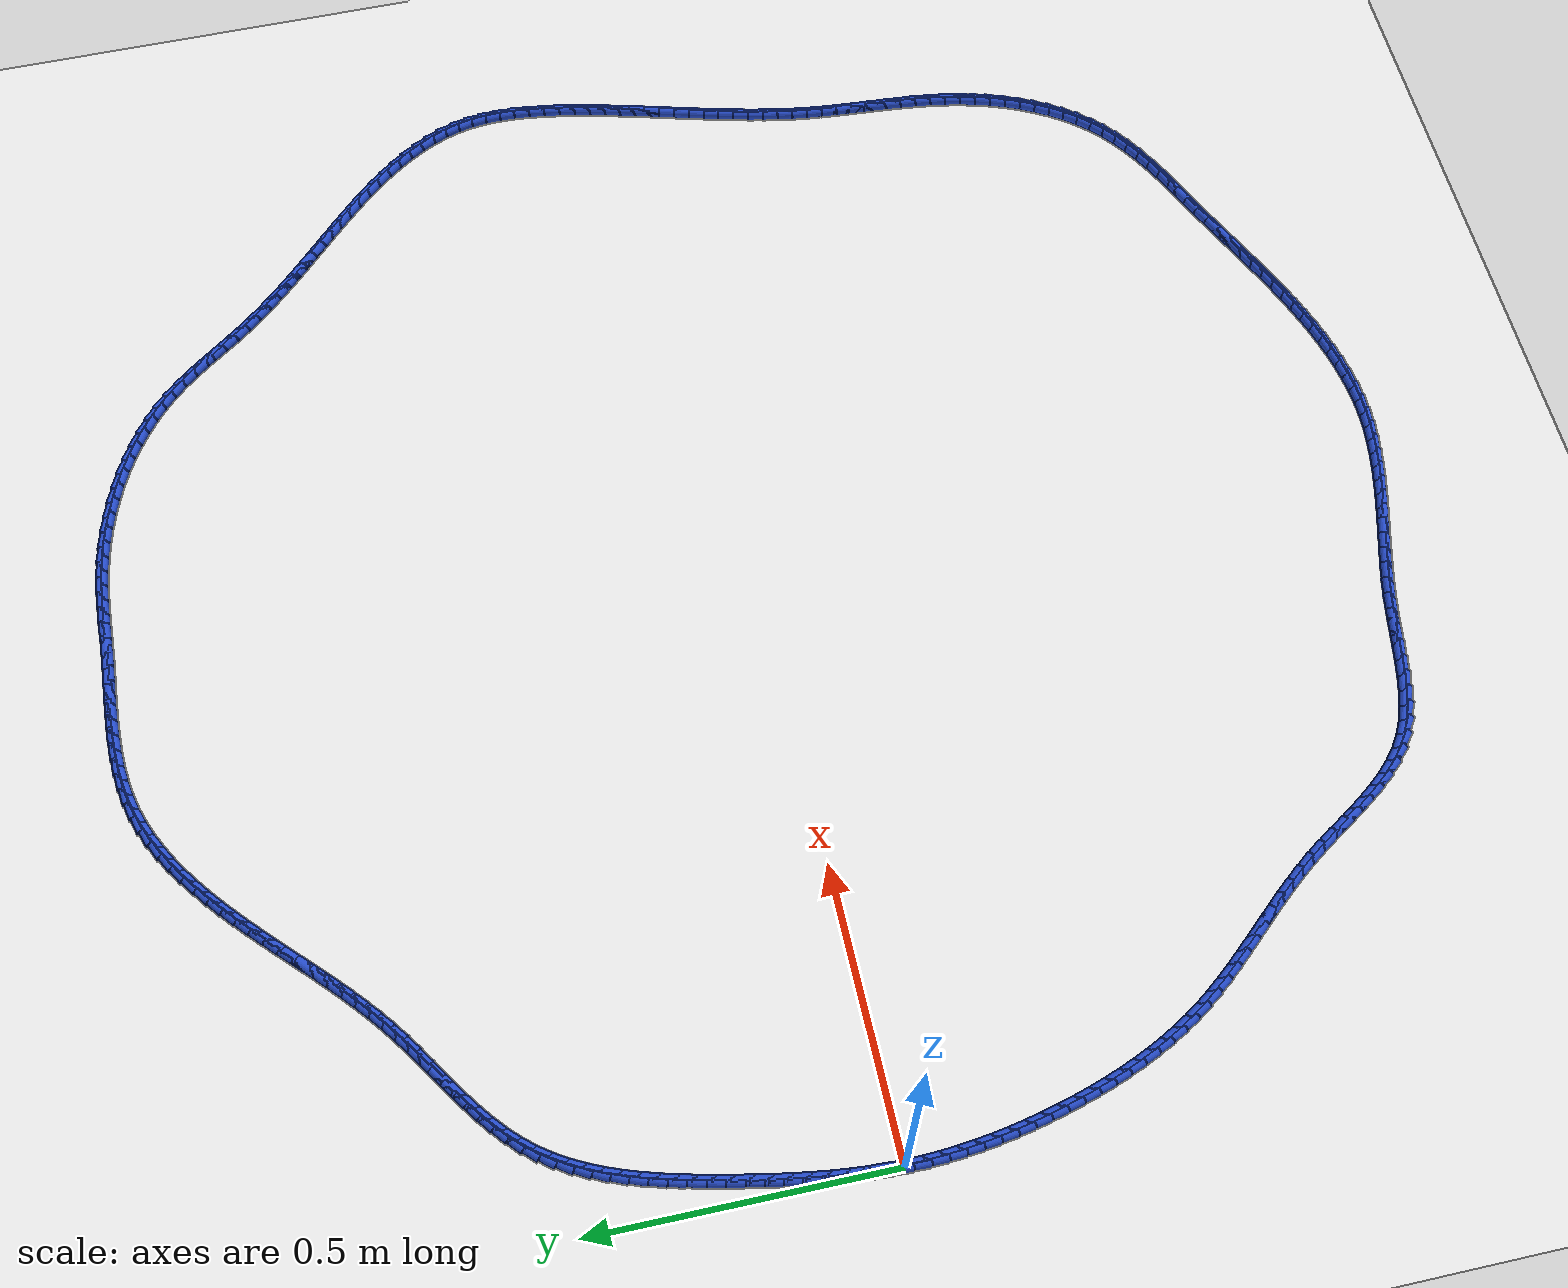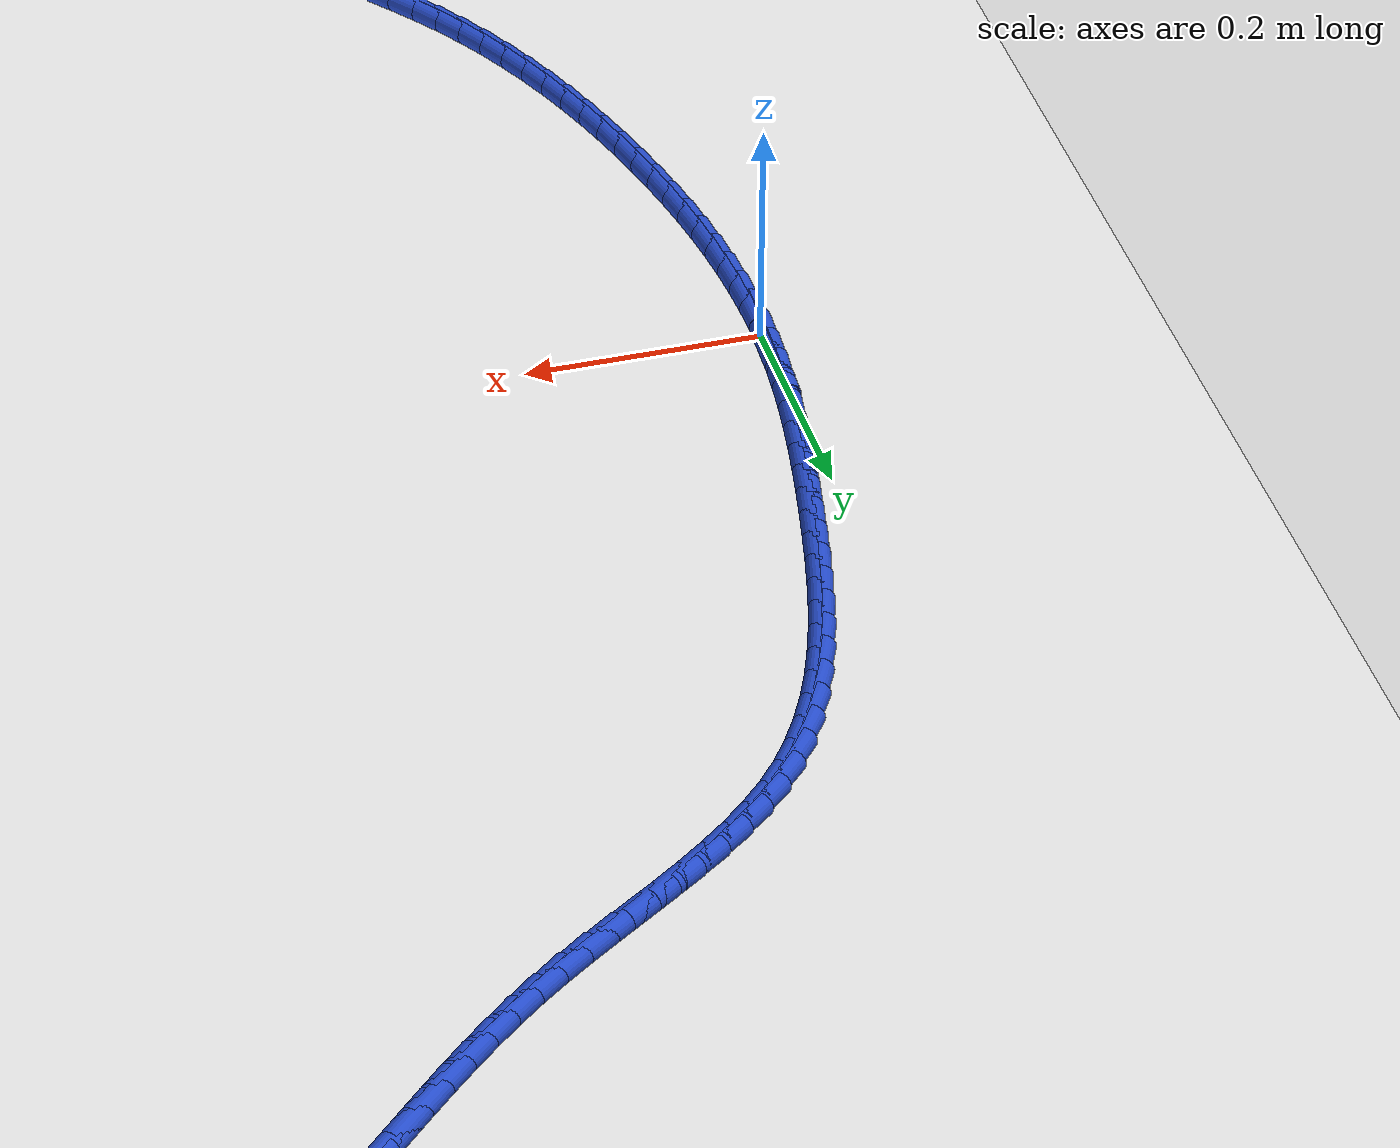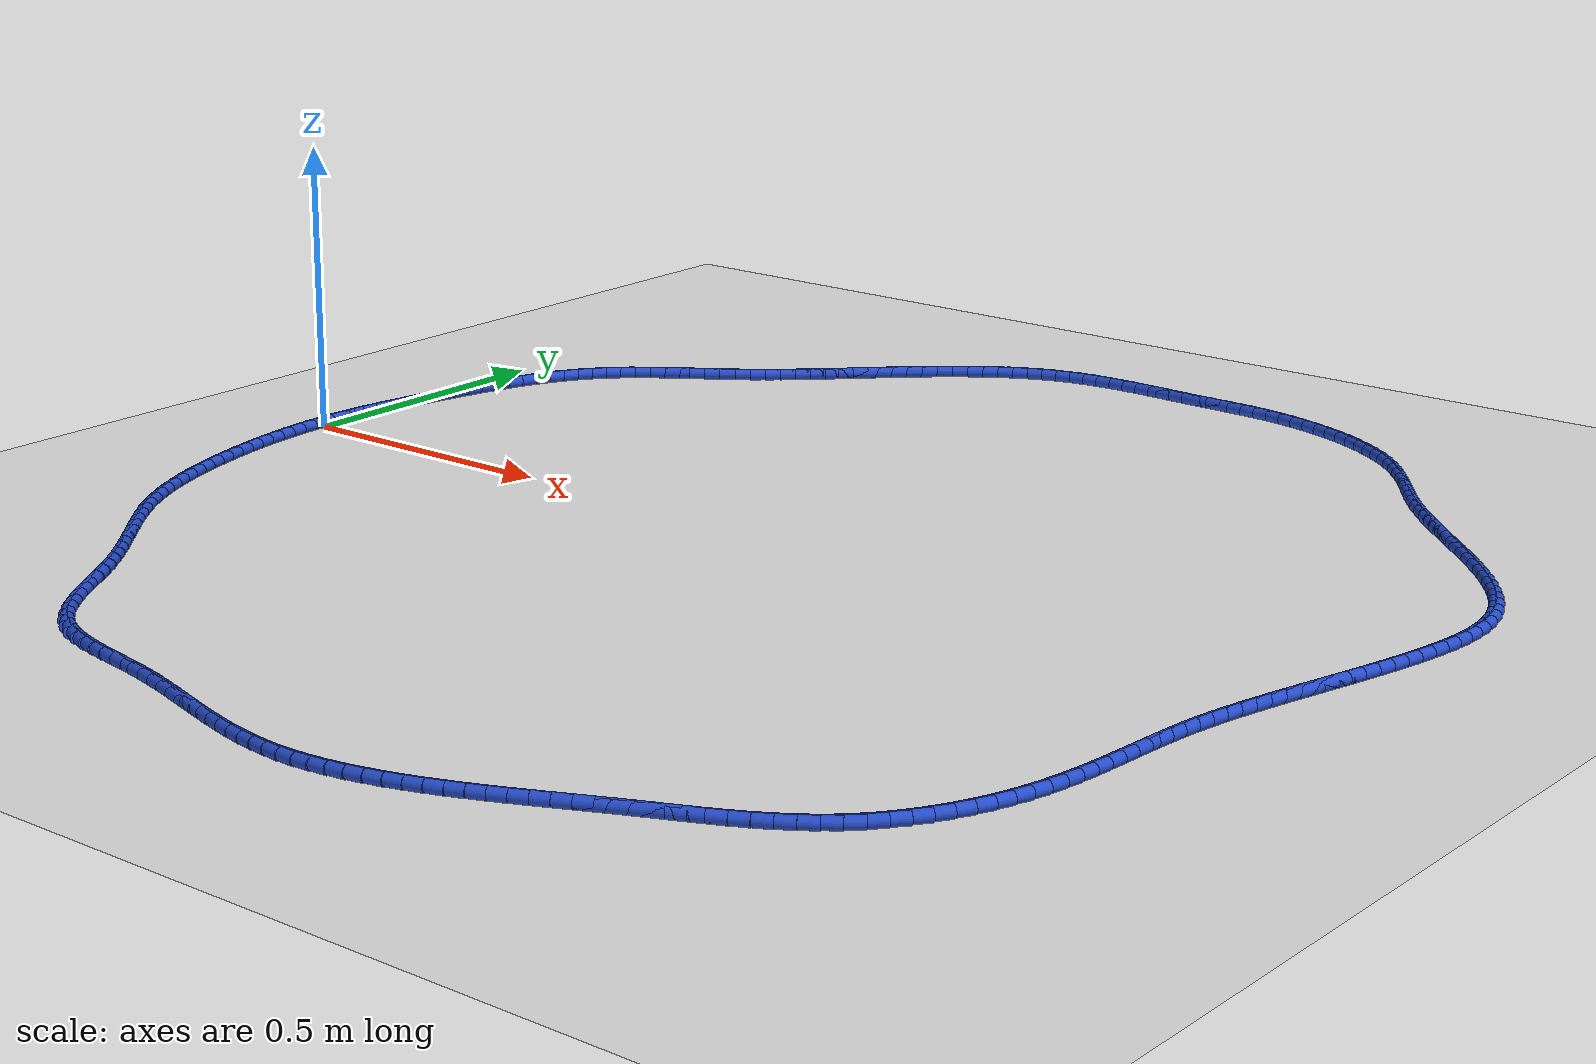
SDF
<sdf version="1.6">
 <world name="default">
  <light name="sun" type="directional">
   <pose>0 0 10 0 -0 0</pose>
   <diffuse>0.8 0.8 0.8 1</diffuse>
   <specular>0.2 0.2 0.2 1</specular>
   <attenuation>
    <range>1000</range>
    <constant>0.9</constant>
    <linear>0.01</linear>
    <quadratic>0.001</quadratic>
   </attenuation>
   <direction>-0.5 0.1 -0.9</direction>
  </light>
  <model name="ground_plane">
   <static>1</static>
   <link name="link">
    <collision name="collision">
     <geometry><plane><normal>0 0 1</normal><size>100 100</size></plane></geometry>
     <surface><friction><ode><mu>100</mu><mu2>50</mu2></ode></friction></surface>
    </collision>
    <visual name="visual">
     <cast_shadows>0</cast_shadows>
     <geometry><plane><normal>0 0 1</normal><size>100 100</size></plane></geometry>
     <material>
      <script><uri>file://media/materials/scripts/gazebo.material</uri><name>Gazebo/WhiteGlow</name></script>
     </material>
    </visual>
   </link>
  </model>
  <gravity>0 0 -9.8</gravity>
  <magnetic_field>6e-06 2.3e-05 -4.2e-05</magnetic_field>
  <atmosphere type="adiabatic"/>
  <physics name="default_physics" default="0" type="ode">
   <max_step_size>0.001</max_step_size>
   <real_time_factor>1</real_time_factor>
   <real_time_update_rate>1000</real_time_update_rate>
  </physics>
  <scene><ambient>0.4 0.4 0.4 1</ambient><background>0.7 0.7 0.7 1</background><shadows>1</shadows></scene>
  <spherical_coordinates>
   <surface_model>EARTH_WGS84</surface_model>
   <latitude_deg>0</latitude_deg>
   <longitude_deg>0</longitude_deg>
   <elevation>0</elevation>
   <heading_deg>0</heading_deg>
  </spherical_coordinates>
  <model name="line">
   <link name="link_0">
    <pose>6.938893903907228e-18 -6.938893903907228e-18 0.01 0 1.57 1.5433155362156543</pose>
    <collision name="collision">
     <geometry><cylinder><radius>0.01</radius><length>0.08</length></cylinder></geometry>
    </collision>
    <visual name="visual">
     <material>
      <script><name>Gazebo/Blue</name><uri>file://media/materials/scripts/gazebo.material</uri></script>
     </material>
     <geometry><cylinder><radius>0.01</radius><length>0.08</length></cylinder></geometry>
    </visual>
   </link>
   <link name="link_1">
    <pose>0.0007640607451513946 0.027796449133164404 0.01 0 1.57 1.51154051715577</pose>
    <collision name="collision">
     <geometry><cylinder><radius>0.01</radius><length>0.08</length></cylinder></geometry>
    </collision>
    <visual name="visual">
     <material>
      <script><name>Gazebo/Blue</name><uri>file://media/materials/scripts/gazebo.material</uri></script>
     </material>
     <geometry><cylinder><radius>0.01</radius><length>0.08</length></cylinder></geometry>
    </visual>
   </link>
   <link name="link_2">
    <pose>0.0024102125542897405 0.05554435577636759 0.01 0 1.57 1.482532509718878</pose>
    <collision name="collision">
     <geometry><cylinder><radius>0.01</radius><length>0.08</length></cylinder></geometry>
    </collision>
    <visual name="visual">
     <material>
      <script><name>Gazebo/Blue</name><uri>file://media/materials/scripts/gazebo.material</uri></script>
     </material>
     <geometry><cylinder><radius>0.01</radius><length>0.08</length></cylinder></geometry>
    </visual>
   </link>
   <link name="link_3">
    <pose>0.00486376748906448 0.08327010149943316 0.01 0 1.57 1.4563945439730883</pose>
    <collision name="collision">
     <geometry><cylinder><radius>0.01</radius><length>0.08</length></cylinder></geometry>
    </collision>
    <visual name="visual">
     <material>
      <script><name>Gazebo/Blue</name><uri>file://media/materials/scripts/gazebo.material</uri></script>
     </material>
     <geometry><cylinder><radius>0.01</radius><length>0.08</length></cylinder></geometry>
    </visual>
   </link>
   <link name="link_4">
    <pose>0.00805003761112504 0.1110000678721846 0.01 0 1.57 1.433190987213368</pose>
    <collision name="collision">
     <geometry><cylinder><radius>0.01</radius><length>0.08</length></cylinder></geometry>
    </collision>
    <visual name="visual">
     <material>
      <script><name>Gazebo/Blue</name><uri>file://media/materials/scripts/gazebo.material</uri></script>
     </material>
     <geometry><cylinder><radius>0.01</radius><length>0.08</length></cylinder></geometry>
    </visual>
   </link>
   <link name="link_5">
    <pose>0.011894334982120863 0.13876063646444547 0.01 0 1.57 1.4129533662033298</pose>
    <collision name="collision">
     <geometry><cylinder><radius>0.01</radius><length>0.08</length></cylinder></geometry>
    </collision>
    <visual name="visual">
     <material>
      <script><name>Gazebo/Blue</name><uri>file://media/materials/scripts/gazebo.material</uri></script>
     </material>
     <geometry><cylinder><radius>0.01</radius><length>0.08</length></cylinder></geometry>
    </visual>
   </link>
   <link name="link_6">
    <pose>0.016321971663701373 0.1665781888460393 0.01 0 1.57 1.3956863175892353</pose>
    <collision name="collision">
     <geometry><cylinder><radius>0.01</radius><length>0.08</length></cylinder></geometry>
    </collision>
    <visual name="visual">
     <material>
      <script><name>Gazebo/Blue</name><uri>file://media/materials/scripts/gazebo.material</uri></script>
     </material>
     <geometry><cylinder><radius>0.01</radius><length>0.08</length></cylinder></geometry>
    </visual>
   </link>
   <link name="link_7">
    <pose>0.02125825971751601 0.19447910658678966 0.01 0 1.57 1.3813732203003999</pose>
    <collision name="collision">
     <geometry><cylinder><radius>0.01</radius><length>0.08</length></cylinder></geometry>
    </collision>
    <visual name="visual">
     <material>
      <script><name>Gazebo/Blue</name><uri>file://media/materials/scripts/gazebo.material</uri></script>
     </material>
     <geometry><cylinder><radius>0.01</radius><length>0.08</length></cylinder></geometry>
    </visual>
   </link>
   <link name="link_8">
    <pose>0.02662851120521419 0.22248977125652 0.01 0 1.57 1.3699812131314013</pose>
    <collision name="collision">
     <geometry><cylinder><radius>0.01</radius><length>0.08</length></cylinder></geometry>
    </collision>
    <visual name="visual">
     <material>
      <script><name>Gazebo/Blue</name><uri>file://media/materials/scripts/gazebo.material</uri></script>
     </material>
     <geometry><cylinder><radius>0.01</radius><length>0.08</length></cylinder></geometry>
    </visual>
   </link>
   <link name="link_9">
    <pose>0.03235803818844536 0.2506365644250539 0.01 0 1.57 1.360956822436799</pose>
    <collision name="collision">
     <geometry><cylinder><radius>0.01</radius><length>0.08</length></cylinder></geometry>
    </collision>
    <visual name="visual">
     <material>
      <script><name>Gazebo/Blue</name><uri>file://media/materials/scripts/gazebo.material</uri></script>
     </material>
     <geometry><cylinder><radius>0.01</radius><length>0.08</length></cylinder></geometry>
    </visual>
   </link>
   <link name="link_10">
    <pose>0.03838496811305587 0.27893537628266835 0.01 0 1.57 1.349193696677252</pose>
    <collision name="collision">
     <geometry><cylinder><radius>0.01</radius><length>0.08</length></cylinder></geometry>
    </collision>
    <visual name="visual">
     <material>
      <script><name>Gazebo/Blue</name><uri>file://media/materials/scripts/gazebo.material</uri></script>
     </material>
     <geometry><cylinder><radius>0.01</radius><length>0.08</length></cylinder></geometry>
    </visual>
   </link>
   <link name="link_11">
    <pose>0.04477505904789802 0.3072976115600427 0.01 0 1.57 1.331719144548799</pose>
    <collision name="collision">
     <geometry><cylinder><radius>0.01</radius><length>0.08</length></cylinder></geometry>
    </collision>
    <visual name="visual">
     <material>
      <script><name>Gazebo/Blue</name><uri>file://media/materials/scripts/gazebo.material</uri></script>
     </material>
     <geometry><cylinder><radius>0.01</radius><length>0.08</length></cylinder></geometry>
    </visual>
   </link>
   <link name="link_12">
    <pose>0.051667291412050544 0.3355747311378937 0.01 0 1.57 1.3083253099618146</pose>
    <collision name="collision">
     <geometry><cylinder><radius>0.01</radius><length>0.08</length></cylinder></geometry>
    </collision>
    <visual name="visual">
     <material>
      <script><name>Gazebo/Blue</name><uri>file://media/materials/scripts/gazebo.material</uri></script>
     </material>
     <geometry><cylinder><radius>0.01</radius><length>0.08</length></cylinder></geometry>
    </visual>
   </link>
   <link name="link_13">
    <pose>0.05920151471333022 0.3636174844130153 0.01 0 1.57 1.2787318895413793</pose>
    <collision name="collision">
     <geometry><cylinder><radius>0.01</radius><length>0.08</length></cylinder></geometry>
    </collision>
    <visual name="visual">
     <material>
      <script><name>Gazebo/Blue</name><uri>file://media/materials/scripts/gazebo.material</uri></script>
     </material>
     <geometry><cylinder><radius>0.01</radius><length>0.08</length></cylinder></geometry>
    </visual>
   </link>
   <link name="link_14">
    <pose>0.06751757845955386 0.3912766207822016 0.01 0 1.57 1.2425681040231191</pose>
    <collision name="collision">
     <geometry><cylinder><radius>0.01</radius><length>0.08</length></cylinder></geometry>
    </collision>
    <visual name="visual">
     <material>
      <script><name>Gazebo/Blue</name><uri>file://media/materials/scripts/gazebo.material</uri></script>
     </material>
     <geometry><cylinder><radius>0.01</radius><length>0.08</length></cylinder></geometry>
    </visual>
   </link>
   <link name="link_15">
    <pose>0.07675533215853834 0.41840288964224703 0.01 0 1.57 1.199397417457635</pose>
    <collision name="collision">
     <geometry><cylinder><radius>0.01</radius><length>0.08</length></cylinder></geometry>
    </collision>
    <visual name="visual">
     <material>
      <script><name>Gazebo/Blue</name><uri>file://media/materials/scripts/gazebo.material</uri></script>
     </material>
     <geometry><cylinder><radius>0.01</radius><length>0.08</length></cylinder></geometry>
    </visual>
   </link>
   <link name="link_16">
    <pose>0.08705462531810049 0.44484704038994594 0.01 0 1.57 1.1487566694844522</pose>
    <collision name="collision">
     <geometry><cylinder><radius>0.01</radius><length>0.08</length></cylinder></geometry>
    </collision>
    <visual name="visual">
     <material>
      <script><name>Gazebo/Blue</name><uri>file://media/materials/scripts/gazebo.material</uri></script>
     </material>
     <geometry><cylinder><radius>0.01</radius><length>0.08</length></cylinder></geometry>
    </visual>
   </link>
   <link name="link_17">
    <pose>0.09855530744605703 0.4704598224220922 0.01 0 1.57 1.090216797764186</pose>
    <collision name="collision">
     <geometry><cylinder><radius>0.01</radius><length>0.08</length></cylinder></geometry>
    </collision>
    <visual name="visual">
     <material>
      <script><name>Gazebo/Blue</name><uri>file://media/materials/scripts/gazebo.material</uri></script>
     </material>
     <geometry><cylinder><radius>0.01</radius><length>0.08</length></cylinder></geometry>
    </visual>
   </link>
   <link name="link_18">
    <pose>0.11139722805022492 0.4950919851354805 0.01 0 1.57 1.0234716447444159</pose>
    <collision name="collision">
     <geometry><cylinder><radius>0.01</radius><length>0.08</length></cylinder></geometry>
    </collision>
    <visual name="visual">
     <material>
      <script><name>Gazebo/Blue</name><uri>file://media/materials/scripts/gazebo.material</uri></script>
     </material>
     <geometry><cylinder><radius>0.01</radius><length>0.08</length></cylinder></geometry>
    </visual>
   </link>
   <link name="link_19">
    <pose>0.1257202366384209 0.5185942779269047 0.01 0 1.57 0.9484567504262988</pose>
    <collision name="collision">
     <geometry><cylinder><radius>0.01</radius><length>0.08</length></cylinder></geometry>
    </collision>
    <visual name="visual">
     <material>
      <script><name>Gazebo/Blue</name><uri>file://media/materials/scripts/gazebo.material</uri></script>
     </material>
     <geometry><cylinder><radius>0.01</radius><length>0.08</length></cylinder></geometry>
    </visual>
   </link>
   <link name="link_20">
    <pose>0.14166418271846182 0.540817450193159 0.01 0 1.57 0.8661796204796266</pose>
    <collision name="collision">
     <geometry><cylinder><radius>0.01</radius><length>0.08</length></cylinder></geometry>
    </collision>
    <visual name="visual">
     <material>
      <script><name>Gazebo/Blue</name><uri>file://media/materials/scripts/gazebo.material</uri></script>
     </material>
     <geometry><cylinder><radius>0.01</radius><length>0.08</length></cylinder></geometry>
    </visual>
   </link>
   <link name="link_21">
    <pose>0.15935500156376364 0.5616250063938173 0.01 0 1.57 0.7880120003795564</pose>
    <collision name="collision">
     <geometry><cylinder><radius>0.01</radius><length>0.08</length></cylinder></geometry>
    </collision>
    <visual name="visual">
     <material>
      <script><name>Gazebo/Blue</name><uri>file://media/materials/scripts/gazebo.material</uri></script>
     </material>
     <geometry><cylinder><radius>0.01</radius><length>0.08</length></cylinder></geometry>
    </visual>
   </link>
   <link name="link_22">
    <pose>0.1787049254737833 0.5810763507246908 0.01 0 1.57 0.7228630505072533</pose>
    <collision name="collision">
     <geometry><cylinder><radius>0.01</radius><length>0.08</length></cylinder></geometry>
    </collision>
    <visual name="visual">
     <material>
      <script><name>Gazebo/Blue</name><uri>file://media/materials/scripts/gazebo.material</uri></script>
     </material>
     <geometry><cylinder><radius>0.01</radius><length>0.08</length></cylinder></geometry>
    </visual>
   </link>
   <link name="link_23">
    <pose>0.19945881610301686 0.5993843146577486 0.01 0 1.57 0.6709122858588802</pose>
    <collision name="collision">
     <geometry><cylinder><radius>0.01</radius><length>0.08</length></cylinder></geometry>
    </collision>
    <visual name="visual">
     <material>
      <script><name>Gazebo/Blue</name><uri>file://media/materials/scripts/gazebo.material</uri></script>
     </material>
     <geometry><cylinder><radius>0.01</radius><length>0.08</length></cylinder></geometry>
    </visual>
   </link>
   <link name="link_24">
    <pose>0.22135706115880383 0.616765830895054 0.01 0 1.57 0.6317341656293107</pose>
    <collision name="collision">
     <geometry><cylinder><radius>0.01</radius><length>0.08</length></cylinder></geometry>
    </collision>
    <visual name="visual">
     <material>
      <script><name>Gazebo/Blue</name><uri>file://media/materials/scripts/gazebo.material</uri></script>
     </material>
     <geometry><cylinder><radius>0.01</radius><length>0.08</length></cylinder></geometry>
    </visual>
   </link>
   <link name="link_25">
    <pose>0.24414004834848338 0.6334378321386702 0.01 0 1.57 0.604787625428781</pose>
    <collision name="collision">
     <geometry><cylinder><radius>0.01</radius><length>0.08</length></cylinder></geometry>
    </collision>
    <visual name="visual">
     <material>
      <script><name>Gazebo/Blue</name><uri>file://media/materials/scripts/gazebo.material</uri></script>
     </material>
     <geometry><cylinder><radius>0.01</radius><length>0.08</length></cylinder></geometry>
    </visual>
   </link>
   <link name="link_26">
    <pose>0.267548165379395 0.6496172510906605 0.01 0 1.57 0.5895932296256344</pose>
    <collision name="collision">
     <geometry><cylinder><radius>0.01</radius><length>0.08</length></cylinder></geometry>
    </collision>
    <visual name="visual">
     <material>
      <script><name>Gazebo/Blue</name><uri>file://media/materials/scripts/gazebo.material</uri></script>
     </material>
     <geometry><cylinder><radius>0.01</radius><length>0.08</length></cylinder></geometry>
    </visual>
   </link>
   <link name="link_27">
    <pose>0.29132179995887814 0.6655210204530883 0.01 0 1.57 0.5858355208060515</pose>
    <collision name="collision">
     <geometry><cylinder><radius>0.01</radius><length>0.08</length></cylinder></geometry>
    </collision>
    <visual name="visual">
     <material>
      <script><name>Gazebo/Blue</name><uri>file://media/materials/scripts/gazebo.material</uri></script>
     </material>
     <geometry><cylinder><radius>0.01</radius><length>0.08</length></cylinder></geometry>
    </visual>
   </link>
   <link name="link_28">
    <pose>0.3152013397942721 0.6813660729280165 0.01 0 1.57 0.5934117138607911</pose>
    <collision name="collision">
     <geometry><cylinder><radius>0.01</radius><length>0.08</length></cylinder></geometry>
    </collision>
    <visual name="visual">
     <material>
      <script><name>Gazebo/Blue</name><uri>file://media/materials/scripts/gazebo.material</uri></script>
     </material>
     <geometry><cylinder><radius>0.01</radius><length>0.08</length></cylinder></geometry>
    </visual>
   </link>
   <link name="link_29">
    <pose>0.3389271725929164 0.6973693412175087 0.01 0 1.57 0.6124413689381945</pose>
    <collision name="collision">
     <geometry><cylinder><radius>0.01</radius><length>0.08</length></cylinder></geometry>
    </collision>
    <visual name="visual">
     <material>
      <script><name>Gazebo/Blue</name><uri>file://media/materials/scripts/gazebo.material</uri></script>
     </material>
     <geometry><cylinder><radius>0.01</radius><length>0.08</length></cylinder></geometry>
    </visual>
   </link>
   <link name="link_30">
    <pose>0.3622396860621504 0.7137477580236282 0.01 0 1.57 0.6428053758617741</pose>
    <collision name="collision">
     <geometry><cylinder><radius>0.01</radius><length>0.08</length></cylinder></geometry>
    </collision>
    <visual name="visual">
     <material>
      <script><name>Gazebo/Blue</name><uri>file://media/materials/scripts/gazebo.material</uri></script>
     </material>
     <geometry><cylinder><radius>0.01</radius><length>0.08</length></cylinder></geometry>
    </visual>
   </link>
   <link name="link_31">
    <pose>0.3848891939982709 0.7307102799243784 0.01 0 1.57 0.6764550343311281</pose>
    <collision name="collision">
     <geometry><cylinder><radius>0.01</radius><length>0.08</length></cylinder></geometry>
    </collision>
    <visual name="visual">
     <material>
      <script><name>Gazebo/Blue</name><uri>file://media/materials/scripts/gazebo.material</uri></script>
     </material>
     <geometry><cylinder><radius>0.01</radius><length>0.08</length></cylinder></geometry>
    </visual>
   </link>
   <link name="link_32">
    <pose>0.4068158436141124 0.7483133225637193 0.01 0 1.57 0.7057310922594642</pose>
    <collision name="collision">
     <geometry><cylinder><radius>0.01</radius><length>0.08</length></cylinder></geometry>
    </collision>
    <visual name="visual">
     <material>
      <script><name>Gazebo/Blue</name><uri>file://media/materials/scripts/gazebo.material</uri></script>
     </material>
     <geometry><cylinder><radius>0.01</radius><length>0.08</length></cylinder></geometry>
    </visual>
   </link>
   <link name="link_33">
    <pose>0.42813042498137377 0.7664761812537211 0.01 0 1.57 0.7301456920130951</pose>
    <collision name="collision">
     <geometry><cylinder><radius>0.01</radius><length>0.08</length></cylinder></geometry>
    </collision>
    <visual name="visual">
     <material>
      <script><name>Gazebo/Blue</name><uri>file://media/materials/scripts/gazebo.material</uri></script>
     </material>
     <geometry><cylinder><radius>0.01</radius><length>0.08</length></cylinder></geometry>
    </visual>
   </link>
   <link name="link_34">
    <pose>0.4489498024783617 0.7851132702880308 0.01 0 1.57 0.7495528673973274</pose>
    <collision name="collision">
     <geometry><cylinder><radius>0.01</radius><length>0.08</length></cylinder></geometry>
    </collision>
    <visual name="visual">
     <material>
      <script><name>Gazebo/Blue</name><uri>file://media/materials/scripts/gazebo.material</uri></script>
     </material>
     <geometry><cylinder><radius>0.01</radius><length>0.08</length></cylinder></geometry>
    </visual>
   </link>
   <link name="link_35">
    <pose>0.46939084048338303 0.8041390039602956 0.01 0 1.57 0.7638675577884524</pose>
    <collision name="collision">
     <geometry><cylinder><radius>0.01</radius><length>0.08</length></cylinder></geometry>
    </collision>
    <visual name="visual">
     <material>
      <script><name>Gazebo/Blue</name><uri>file://media/materials/scripts/gazebo.material</uri></script>
     </material>
     <geometry><cylinder><radius>0.01</radius><length>0.08</length></cylinder></geometry>
    </visual>
   </link>
   <link name="link_36">
    <pose>0.4895704033747442 0.8234677965641624 0.01 0 1.57 0.7730523710438469</pose>
    <collision name="collision">
     <geometry><cylinder><radius>0.01</radius><length>0.08</length></cylinder></geometry>
    </collision>
    <visual name="visual">
     <material>
      <script><name>Gazebo/Blue</name><uri>file://media/materials/scripts/gazebo.material</uri></script>
     </material>
     <geometry><cylinder><radius>0.01</radius><length>0.08</length></cylinder></geometry>
    </visual>
   </link>
   <link name="link_37">
    <pose>0.5096053555307523 0.8430140623932777 0.01 0 1.57 0.7771068207561972</pose>
    <collision name="collision">
     <geometry><cylinder><radius>0.01</radius><length>0.08</length></cylinder></geometry>
    </collision>
    <visual name="visual">
     <material>
      <script><name>Gazebo/Blue</name><uri>file://media/materials/scripts/gazebo.material</uri></script>
     </material>
     <geometry><cylinder><radius>0.01</radius><length>0.08</length></cylinder></geometry>
    </visual>
   </link>
   <link name="link_38">
    <pose>0.5296125613297132 0.8626922157412891 0.01 0 1.57 0.7760598767116107</pose>
    <collision name="collision">
     <geometry><cylinder><radius>0.01</radius><length>0.08</length></cylinder></geometry>
    </collision>
    <visual name="visual">
     <material>
      <script><name>Gazebo/Blue</name><uri>file://media/materials/scripts/gazebo.material</uri></script>
     </material>
     <geometry><cylinder><radius>0.01</radius><length>0.08</length></cylinder></geometry>
    </visual>
   </link>
   <link name="link_39">
    <pose>0.5497088851499345 0.8824166709018433 0.01 0 1.57 0.7699661831465208</pose>
    <collision name="collision">
     <geometry><cylinder><radius>0.01</radius><length>0.08</length></cylinder></geometry>
    </collision>
    <visual name="visual">
     <material>
      <script><name>Gazebo/Blue</name><uri>file://media/materials/scripts/gazebo.material</uri></script>
     </material>
     <geometry><cylinder><radius>0.01</radius><length>0.08</length></cylinder></geometry>
    </visual>
   </link>
   <link name="link_40">
    <pose>0.570011191369722 0.9021018421685866 0.01 0 1.57 0.7589059360338442</pose>
    <collision name="collision">
     <geometry><cylinder><radius>0.01</radius><length>0.08</length></cylinder></geometry>
    </collision>
    <visual name="visual">
     <material>
      <script><name>Gazebo/Blue</name><uri>file://media/materials/scripts/gazebo.material</uri></script>
     </material>
     <geometry><cylinder><radius>0.01</radius><length>0.08</length></cylinder></geometry>
    </visual>
   </link>
   <link name="link_41">
    <pose>0.5906363443673828 0.9216621438351669 0.01 0 1.57 0.7429858804503433</pose>
    <collision name="collision">
     <geometry><cylinder><radius>0.01</radius><length>0.08</length></cylinder></geometry>
    </collision>
    <visual name="visual">
     <material>
      <script><name>Gazebo/Blue</name><uri>file://media/materials/scripts/gazebo.material</uri></script>
     </material>
     <geometry><cylinder><radius>0.01</radius><length>0.08</length></cylinder></geometry>
    </visual>
   </link>
   <link name="link_42">
    <pose>0.6117003586816455 0.9410111224008926 0.01 0 1.57 0.7221931312060554</pose>
    <collision name="collision">
     <geometry><cylinder><radius>0.01</radius><length>0.08</length></cylinder></geometry>
    </collision>
    <visual name="visual">
     <material>
      <script><name>Gazebo/Blue</name><uri>file://media/materials/scripts/gazebo.material</uri></script>
     </material>
     <geometry><cylinder><radius>0.01</radius><length>0.08</length></cylinder></geometry>
    </visual>
   </link>
   <link name="link_43">
    <pose>0.6332770142599757 0.9600191974737042 0.01 0 1.57 0.6962564531004632</pose>
    <collision name="collision">
     <geometry><cylinder><radius>0.01</radius><length>0.08</length></cylinder></geometry>
    </collision>
    <visual name="visual">
     <material>
      <script><name>Gazebo/Blue</name><uri>file://media/materials/scripts/gazebo.material</uri></script>
     </material>
     <geometry><cylinder><radius>0.01</radius><length>0.08</length></cylinder></geometry>
    </visual>
   </link>
   <link name="link_44">
    <pose>0.6553792196328615 0.9784946311998747 0.01 0 1.57 0.6648988855503468</pose>
    <collision name="collision">
     <geometry><cylinder><radius>0.01</radius><length>0.08</length></cylinder></geometry>
    </collision>
    <visual name="visual">
     <material>
      <script><name>Gazebo/Blue</name><uri>file://media/materials/scripts/gazebo.material</uri></script>
     </material>
     <geometry><cylinder><radius>0.01</radius><length>0.08</length></cylinder></geometry>
    </visual>
   </link>
   <link name="link_45">
    <pose>0.6780151493059452 0.9962408516839789 0.01 0 1.57 0.6277749286086561</pose>
    <collision name="collision">
     <geometry><cylinder><radius>0.01</radius><length>0.08</length></cylinder></geometry>
    </collision>
    <visual name="visual">
     <material>
      <script><name>Gazebo/Blue</name><uri>file://media/materials/scripts/gazebo.material</uri></script>
     </material>
     <geometry><cylinder><radius>0.01</radius><length>0.08</length></cylinder></geometry>
    </visual>
   </link>
   <link name="link_46">
    <pose>0.7011929777848681 1.0130612870305913 0.01 0 1.57 0.5844778655012535</pose>
    <collision name="collision">
     <geometry><cylinder><radius>0.01</radius><length>0.08</length></cylinder></geometry>
    </collision>
    <visual name="visual">
     <material>
      <script><name>Gazebo/Blue</name><uri>file://media/materials/scripts/gazebo.material</uri></script>
     </material>
     <geometry><cylinder><radius>0.01</radius><length>0.08</length></cylinder></geometry>
    </visual>
   </link>
   <link name="link_47">
    <pose>0.7249208795752735 1.0287593653442872 0.01 0 1.57 0.5345697009971386</pose>
    <collision name="collision">
     <geometry><cylinder><radius>0.01</radius><length>0.08</length></cylinder></geometry>
    </collision>
    <visual name="visual">
     <material>
      <script><name>Gazebo/Blue</name><uri>file://media/materials/scripts/gazebo.material</uri></script>
     </material>
     <geometry><cylinder><radius>0.01</radius><length>0.08</length></cylinder></geometry>
    </visual>
   </link>
   <link name="link_48">
    <pose>0.7492070291828022 1.0431385147296406 0.01 0 1.57 0.4776269136732679</pose>
    <collision name="collision">
     <geometry><cylinder><radius>0.01</radius><length>0.08</length></cylinder></geometry>
    </collision>
    <visual name="visual">
     <material>
      <script><name>Gazebo/Blue</name><uri>file://media/materials/scripts/gazebo.material</uri></script>
     </material>
     <geometry><cylinder><radius>0.01</radius><length>0.08</length></cylinder></geometry>
    </visual>
   </link>
   <link name="link_49">
    <pose>0.7740596011130966 1.056002163291227 0.01 0 1.57 0.41330760777728537</pose>
    <collision name="collision">
     <geometry><cylinder><radius>0.01</radius><length>0.08</length></cylinder></geometry>
    </collision>
    <visual name="visual">
     <material>
      <script><name>Gazebo/Blue</name><uri>file://media/materials/scripts/gazebo.material</uri></script>
     </material>
     <geometry><cylinder><radius>0.01</radius><length>0.08</length></cylinder></geometry>
    </visual>
   </link>
   <link name="link_50">
    <pose>0.7994867698717989 1.0671537391336208 0.01 0 1.57 0.3414432003201853</pose>
    <collision name="collision">
     <geometry><cylinder><radius>0.01</radius><length>0.08</length></cylinder></geometry>
    </collision>
    <visual name="visual">
     <material>
      <script><name>Gazebo/Blue</name><uri>file://media/materials/scripts/gazebo.material</uri></script>
     </material>
     <geometry><cylinder><radius>0.01</radius><length>0.08</length></cylinder></geometry>
    </visual>
   </link>
   <link name="link_51">
    <pose>0.8254967099645506 1.076396670361396 0.01 0 1.57 0.2639546696373786</pose>
    <collision name="collision">
     <geometry><cylinder><radius>0.01</radius><length>0.08</length></cylinder></geometry>
    </collision>
    <visual name="visual">
     <material>
      <script><name>Gazebo/Blue</name><uri>file://media/materials/scripts/gazebo.material</uri></script>
     </material>
     <geometry><cylinder><radius>0.01</radius><length>0.08</length></cylinder></geometry>
    </visual>
   </link>
   <link name="link_52">
    <pose>0.8520881940674213 1.0835832996119266 0.01 0 1.57 0.19201581246392607</pose>
    <collision name="collision">
     <geometry><cylinder><radius>0.01</radius><length>0.08</length></cylinder></geometry>
    </collision>
    <visual name="visual">
     <material>
      <script><name>Gazebo/Blue</name><uri>file://media/materials/scripts/gazebo.material</uri></script>
     </material>
     <geometry><cylinder><radius>0.01</radius><length>0.08</length></cylinder></geometry>
    </visual>
   </link>
   <link name="link_53">
    <pose>0.879204441094795 1.08885499691632 0.01 0 1.57 0.1300101135953835</pose>
    <collision name="collision">
     <geometry><cylinder><radius>0.01</radius><length>0.08</length></cylinder></geometry>
    </collision>
    <visual name="visual">
     <material>
      <script><name>Gazebo/Blue</name><uri>file://media/materials/scripts/gazebo.material</uri></script>
     </material>
     <geometry><cylinder><radius>0.01</radius><length>0.08</length></cylinder></geometry>
    </visual>
   </link>
   <link name="link_54">
    <pose>0.9067683384127583 1.0924589104607076 0.01 0 1.57 0.07800437647326312</pose>
    <collision name="collision">
     <geometry><cylinder><radius>0.01</radius><length>0.08</length></cylinder></geometry>
    </collision>
    <visual name="visual">
     <material>
      <script><name>Gazebo/Blue</name><uri>file://media/materials/scripts/gazebo.material</uri></script>
     </material>
     <geometry><cylinder><radius>0.01</radius><length>0.08</length></cylinder></geometry>
    </visual>
   </link>
   <link name="link_55">
    <pose>0.9347027429907334 1.0946423465747617 0.01 0 1.57 0.03577448857978379</pose>
    <collision name="collision">
     <geometry><cylinder><radius>0.01</radius><length>0.08</length></cylinder></geometry>
    </collision>
    <visual name="visual">
     <material>
      <script><name>Gazebo/Blue</name><uri>file://media/materials/scripts/gazebo.material</uri></script>
     </material>
     <geometry><cylinder><radius>0.01</radius><length>0.08</length></cylinder></geometry>
    </visual>
   </link>
   <link name="link_56">
    <pose>0.9629305117981425 1.095652611588152 0.01 0 1.57 0.002967234719183303</pose>
    <collision name="collision">
     <geometry><cylinder><radius>0.01</radius><length>0.08</length></cylinder></geometry>
    </collision>
    <visual name="visual">
     <material>
      <script><name>Gazebo/Blue</name><uri>file://media/materials/scripts/gazebo.material</uri></script>
     </material>
     <geometry><cylinder><radius>0.01</radius><length>0.08</length></cylinder></geometry>
    </visual>
   </link>
   <link name="link_57">
    <pose>0.991374501804408 1.095737011830551 0.01 0 1.57 -0.020784075329159046</pose>
    <collision name="collision">
     <geometry><cylinder><radius>0.01</radius><length>0.08</length></cylinder></geometry>
    </collision>
    <visual name="visual">
     <material>
      <script><name>Gazebo/Blue</name><uri>file://media/materials/scripts/gazebo.material</uri></script>
     </material>
     <geometry><cylinder><radius>0.01</radius><length>0.08</length></cylinder></geometry>
    </visual>
   </link>
   <link name="link_58">
    <pose>1.0199575699789516 1.0951428536316274 0.01 0 1.57 -0.035781900107793495</pose>
    <collision name="collision">
     <geometry><cylinder><radius>0.01</radius><length>0.08</length></cylinder></geometry>
    </collision>
    <visual name="visual">
     <material>
      <script><name>Gazebo/Blue</name><uri>file://media/materials/scripts/gazebo.material</uri></script>
     </material>
     <geometry><cylinder><radius>0.01</radius><length>0.08</length></cylinder></geometry>
    </visual>
   </link>
   <link name="link_59">
    <pose>1.0486025732911959 1.0941174433210548 0.01 0 1.57 -0.04221607428798749</pose>
    <collision name="collision">
     <geometry><cylinder><radius>0.01</radius><length>0.08</length></cylinder></geometry>
    </collision>
    <visual name="visual">
     <material>
      <script><name>Gazebo/Blue</name><uri>file://media/materials/scripts/gazebo.material</uri></script>
     </material>
     <geometry><cylinder><radius>0.01</radius><length>0.08</length></cylinder></geometry>
    </visual>
   </link>
   <link name="link_60">
    <pose>1.0772323687105632 1.0929080872285022 0.01 0 1.57 -0.0401360436025834</pose>
    <collision name="collision">
     <geometry><cylinder><radius>0.01</radius><length>0.08</length></cylinder></geometry>
    </collision>
    <visual name="visual">
     <material>
      <script><name>Gazebo/Blue</name><uri>file://media/materials/scripts/gazebo.material</uri></script>
     </material>
     <geometry><cylinder><radius>0.01</radius><length>0.08</length></cylinder></geometry>
    </visual>
   </link>
   <link name="link_61">
    <pose>1.1057698132064757 1.0917620916836417 0.01 0 1.57 -0.02960711799082537</pose>
    <collision name="collision">
     <geometry><cylinder><radius>0.01</radius><length>0.08</length></cylinder></geometry>
    </collision>
    <visual name="visual">
     <material>
      <script><name>Gazebo/Blue</name><uri>file://media/materials/scripts/gazebo.material</uri></script>
     </material>
     <geometry><cylinder><radius>0.01</radius><length>0.08</length></cylinder></geometry>
    </visual>
   </link>
   <link name="link_62">
    <pose>1.1341389333476963 1.0909219182885102 0.01 0 1.57 -0.018696714109490135</pose>
    <collision name="collision">
     <geometry><cylinder><radius>0.01</radius><length>0.08</length></cylinder></geometry>
    </collision>
    <visual name="visual">
     <material>
      <script><name>Gazebo/Blue</name><uri>file://media/materials/scripts/gazebo.material</uri></script>
     </material>
     <geometry><cylinder><radius>0.01</radius><length>0.08</length></cylinder></geometry>
    </visual>
   </link>
   <link name="link_63">
    <pose>1.1623205066900044 1.0903949540640205 0.01 0 1.57 -0.019313266174215596</pose>
    <collision name="collision">
     <geometry><cylinder><radius>0.01</radius><length>0.08</length></cylinder></geometry>
    </collision>
    <visual name="visual">
     <material>
      <script><name>Gazebo/Blue</name><uri>file://media/materials/scripts/gazebo.material</uri></script>
     </material>
     <geometry><cylinder><radius>0.01</radius><length>0.08</length></cylinder></geometry>
    </visual>
   </link>
   <link name="link_64">
    <pose>1.1903763179303777 1.089853037333406 0.01 0 1.57 -0.032518358520695255</pose>
    <collision name="collision">
     <geometry><cylinder><radius>0.01</radius><length>0.08</length></cylinder></geometry>
    </collision>
    <visual name="visual">
     <material>
      <script><name>Gazebo/Blue</name><uri>file://media/materials/scripts/gazebo.material</uri></script>
     </material>
     <geometry><cylinder><radius>0.01</radius><length>0.08</length></cylinder></geometry>
    </visual>
   </link>
   <link name="link_65">
    <pose>1.2183743660079622 1.0889422657156207 0.01 0 1.57 -0.058257066828256696</pose>
    <collision name="collision">
     <geometry><cylinder><radius>0.01</radius><length>0.08</length></cylinder></geometry>
    </collision>
    <visual name="visual">
     <material>
      <script><name>Gazebo/Blue</name><uri>file://media/materials/scripts/gazebo.material</uri></script>
     </material>
     <geometry><cylinder><radius>0.01</radius><length>0.08</length></cylinder></geometry>
    </visual>
   </link>
   <link name="link_66">
    <pose>1.2463826498619033 1.0873087368296181 0.01 0 1.57 -0.09613697446471628</pose>
    <collision name="collision">
     <geometry><cylinder><radius>0.01</radius><length>0.08</length></cylinder></geometry>
    </collision>
    <visual name="visual">
     <material>
      <script><name>Gazebo/Blue</name><uri>file://media/materials/scripts/gazebo.material</uri></script>
     </material>
     <geometry><cylinder><radius>0.01</radius><length>0.08</length></cylinder></geometry>
    </visual>
   </link>
   <link name="link_67">
    <pose>1.274468266371643 1.0846003214747972 0.01 0 1.57 -0.1413670093650362</pose>
    <collision name="collision">
     <geometry><cylinder><radius>0.01</radius><length>0.08</length></cylinder></geometry>
    </collision>
    <visual name="visual">
     <material>
      <script><name>Gazebo/Blue</name><uri>file://media/materials/scripts/gazebo.material</uri></script>
     </material>
     <geometry><cylinder><radius>0.01</radius><length>0.08</length></cylinder></geometry>
    </visual>
   </link>
   <link name="link_68">
    <pose>1.3026336882772702 1.080591922242199 0.01 0 1.57 -0.18696988690290806</pose>
    <collision name="collision">
     <geometry><cylinder><radius>0.01</radius><length>0.08</length></cylinder></geometry>
    </collision>
    <visual name="visual">
     <material>
      <script><name>Gazebo/Blue</name><uri>file://media/materials/scripts/gazebo.material</uri></script>
     </material>
     <geometry><cylinder><radius>0.01</radius><length>0.08</length></cylinder></geometry>
    </visual>
   </link>
   <link name="link_69">
    <pose>1.330774665438915 1.0752682270876732 0.01 0 1.57 -0.23264285344873262</pose>
    <collision name="collision">
     <geometry><cylinder><radius>0.01</radius><length>0.08</length></cylinder></geometry>
    </collision>
    <visual name="visual">
     <material>
      <script><name>Gazebo/Blue</name><uri>file://media/materials/scripts/gazebo.material</uri></script>
     </material>
     <geometry><cylinder><radius>0.01</radius><length>0.08</length></cylinder></geometry>
    </visual>
   </link>
   <link name="link_70">
    <pose>1.3587769558761416 1.0686335649467695 0.01 0 1.57 -0.2787297673906005</pose>
    <collision name="collision">
     <geometry><cylinder><radius>0.01</radius><length>0.08</length></cylinder></geometry>
    </collision>
    <visual name="visual">
     <material>
      <script><name>Gazebo/Blue</name><uri>file://media/materials/scripts/gazebo.material</uri></script>
     </material>
     <geometry><cylinder><radius>0.01</radius><length>0.08</length></cylinder></geometry>
    </visual>
   </link>
   <link name="link_71">
    <pose>1.386526317608513 1.0606922647550359 0.01 0 1.57 -0.32556535346390403</pose>
    <collision name="collision">
     <geometry><cylinder><radius>0.01</radius><length>0.08</length></cylinder></geometry>
    </collision>
    <visual name="visual">
     <material>
      <script><name>Gazebo/Blue</name><uri>file://media/materials/scripts/gazebo.material</uri></script>
     </material>
     <geometry><cylinder><radius>0.01</radius><length>0.08</length></cylinder></geometry>
    </visual>
   </link>
   <link name="link_72">
    <pose>1.4139085086555927 1.0514486554480214 0.01 0 1.57 -0.3734775712281659</pose>
    <collision name="collision">
     <geometry><cylinder><radius>0.01</radius><length>0.08</length></cylinder></geometry>
    </collision>
    <visual name="visual">
     <material>
      <script><name>Gazebo/Blue</name><uri>file://media/materials/scripts/gazebo.material</uri></script>
     </material>
     <geometry><cylinder><radius>0.01</radius><length>0.08</length></cylinder></geometry>
    </visual>
   </link>
   <link name="link_73">
    <pose>1.440809287036945 1.0409070659612738 0.01 0 1.57 -0.4227886436230414</pose>
    <collision name="collision">
     <geometry><cylinder><radius>0.01</radius><length>0.08</length></cylinder></geometry>
    </collision>
    <visual name="visual">
     <material>
      <script><name>Gazebo/Blue</name><uri>file://media/materials/scripts/gazebo.material</uri></script>
     </material>
     <geometry><cylinder><radius>0.01</radius><length>0.08</length></cylinder></geometry>
    </visual>
   </link>
   <link name="link_74">
    <pose>1.467114410772133 1.029071825230342 0.01 0 1.57 -0.47381438603906895</pose>
    <collision name="collision">
     <geometry><cylinder><radius>0.01</radius><length>0.08</length></cylinder></geometry>
    </collision>
    <visual name="visual">
     <material>
      <script><name>Gazebo/Blue</name><uri>file://media/materials/scripts/gazebo.material</uri></script>
     </material>
     <geometry><cylinder><radius>0.01</radius><length>0.08</length></cylinder></geometry>
    </visual>
   </link>
   <link name="link_75">
    <pose>1.4927096378807205 1.0159472621907746 0.01 0 1.57 -0.5268613911210545</pose>
    <collision name="collision">
     <geometry><cylinder><radius>0.01</radius><length>0.08</length></cylinder></geometry>
    </collision>
    <visual name="visual">
     <material>
      <script><name>Gazebo/Blue</name><uri>file://media/materials/scripts/gazebo.material</uri></script>
     </material>
     <geometry><cylinder><radius>0.01</radius><length>0.08</length></cylinder></geometry>
    </visual>
   </link>
   <link name="link_76">
    <pose>1.517480726382271 1.00153770577812 0.01 0 1.57 -0.5822215484820027</pose>
    <collision name="collision">
     <geometry><cylinder><radius>0.01</radius><length>0.08</length></cylinder></geometry>
    </collision>
    <visual name="visual">
     <material>
      <script><name>Gazebo/Blue</name><uri>file://media/materials/scripts/gazebo.material</uri></script>
     </material>
     <geometry><cylinder><radius>0.01</radius><length>0.08</length></cylinder></geometry>
    </visual>
   </link>
   <link name="link_77">
    <pose>1.5413134342963484 0.9858474849279267 0.01 0 1.57 -0.6401633476710498</pose>
    <collision name="collision">
     <geometry><cylinder><radius>0.01</radius><length>0.08</length></cylinder></geometry>
    </collision>
    <visual name="visual">
     <material>
      <script><name>Gazebo/Blue</name><uri>file://media/materials/scripts/gazebo.material</uri></script>
     </material>
     <geometry><cylinder><radius>0.01</radius><length>0.08</length></cylinder></geometry>
    </visual>
   </link>
   <link name="link_78">
    <pose>1.5640935196425159 0.968880928575743 0.01 0 1.57 -0.7009194819324006</pose>
    <collision name="collision">
     <geometry><cylinder><radius>0.01</radius><length>0.08</length></cylinder></geometry>
    </collision>
    <visual name="visual">
     <material>
      <script><name>Gazebo/Blue</name><uri>file://media/materials/scripts/gazebo.material</uri></script>
     </material>
     <geometry><cylinder><radius>0.01</radius><length>0.08</length></cylinder></geometry>
    </visual>
   </link>
   <link name="link_79">
    <pose>1.5857067404403375 0.9506423656571178 0.01 0 1.57 -0.764653347204239</pose>
    <collision name="collision">
     <geometry><cylinder><radius>0.01</radius><length>0.08</length></cylinder></geometry>
    </collision>
    <visual name="visual">
     <material>
      <script><name>Gazebo/Blue</name><uri>file://media/materials/scripts/gazebo.material</uri></script>
     </material>
     <geometry><cylinder><radius>0.01</radius><length>0.08</length></cylinder></geometry>
    </visual>
   </link>
   <link name="link_80">
    <pose>1.6060392605332807 0.9311364060752363 0.01 0 1.57 -0.8267359838469015</pose>
    <collision name="collision">
     <geometry><cylinder><radius>0.01</radius><length>0.08</length></cylinder></geometry>
    </collision>
    <visual name="visual">
     <material>
      <script><name>Gazebo/Blue</name><uri>file://media/materials/scripts/gazebo.material</uri></script>
     </material>
     <geometry><cylinder><radius>0.01</radius><length>0.08</length></cylinder></geometry>
    </visual>
   </link>
   <link name="link_81">
    <pose>1.625087760354476 0.9104441746568968 0.01 0 1.57 -0.8758821805450064</pose>
    <collision name="collision">
     <geometry><cylinder><radius>0.01</radius><length>0.08</length></cylinder></geometry>
    </collision>
    <visual name="visual">
     <material>
      <script><name>Gazebo/Blue</name><uri>file://media/materials/scripts/gazebo.material</uri></script>
     </material>
     <geometry><cylinder><radius>0.01</radius><length>0.08</length></cylinder></geometry>
    </visual>
   </link>
   <link name="link_82">
    <pose>1.64310876706386 0.888826698201205 0.01 0 1.57 -0.9103907295612471</pose>
    <collision name="collision">
     <geometry><cylinder><radius>0.01</radius><length>0.08</length></cylinder></geometry>
    </collision>
    <visual name="visual">
     <material>
      <script><name>Gazebo/Blue</name><uri>file://media/materials/scripts/gazebo.material</uri></script>
     </material>
     <geometry><cylinder><radius>0.01</radius><length>0.08</length></cylinder></geometry>
    </visual>
   </link>
   <link name="link_83">
    <pose>1.6603961197752557 0.8665708360208296 0.01 0 1.57 -0.930359745719579</pose>
    <collision name="collision">
     <geometry><cylinder><radius>0.01</radius><length>0.08</length></cylinder></geometry>
    </collision>
    <visual name="visual">
     <material>
      <script><name>Gazebo/Blue</name><uri>file://media/materials/scripts/gazebo.material</uri></script>
     </material>
     <geometry><cylinder><radius>0.01</radius><length>0.08</length></cylinder></geometry>
    </visual>
   </link>
   <link name="link_84">
    <pose>1.6772436576024878 0.8439634474284402 0.01 0 1.57 -0.9358886128954762</pose>
    <collision name="collision">
     <geometry><cylinder><radius>0.01</radius><length>0.08</length></cylinder></geometry>
    </collision>
    <visual name="visual">
     <material>
      <script><name>Gazebo/Blue</name><uri>file://media/materials/scripts/gazebo.material</uri></script>
     </material>
     <geometry><cylinder><radius>0.01</radius><length>0.08</length></cylinder></geometry>
    </visual>
   </link>
   <link name="link_85">
    <pose>1.69394521965938 0.8212913917367056 0.01 0 1.57 -0.9269524182687914</pose>
    <collision name="collision">
     <geometry><cylinder><radius>0.01</radius><length>0.08</length></cylinder></geometry>
    </collision>
    <visual name="visual">
     <material>
      <script><name>Gazebo/Blue</name><uri>file://media/materials/scripts/gazebo.material</uri></script>
     </material>
     <geometry><cylinder><radius>0.01</radius><length>0.08</length></cylinder></geometry>
    </visual>
   </link>
   <link name="link_86">
    <pose>1.7107946450597553 0.7988415282582952 0.01 0 1.57 -0.9033989431904076</pose>
    <collision name="collision">
     <geometry><cylinder><radius>0.01</radius><length>0.08</length></cylinder></geometry>
    </collision>
    <visual name="visual">
     <material>
      <script><name>Gazebo/Blue</name><uri>file://media/materials/scripts/gazebo.material</uri></script>
     </material>
     <geometry><cylinder><radius>0.01</radius><length>0.08</length></cylinder></geometry>
    </visual>
   </link>
   <link name="link_87">
    <pose>1.7280851609996637 0.7768999923186831 0.01 0 1.57 -0.8706474445221448</pose>
    <collision name="collision">
     <geometry><cylinder><radius>0.01</radius><length>0.08</length></cylinder></geometry>
    </collision>
    <visual name="visual">
     <material>
      <script><name>Gazebo/Blue</name><uri>file://media/materials/scripts/gazebo.material</uri></script>
     </material>
     <geometry><cylinder><radius>0.01</radius><length>0.08</length></cylinder></geometry>
    </visual>
   </link>
   <link name="link_88">
    <pose>1.7460060725045823 0.7556299642907484 0.01 0 1.57 -0.8408210769825334</pose>
    <collision name="collision">
     <geometry><cylinder><radius>0.01</radius><length>0.08</length></cylinder></geometry>
    </collision>
    <visual name="visual">
     <material>
      <script><name>Gazebo/Blue</name><uri>file://media/materials/scripts/gazebo.material</uri></script>
     </material>
     <geometry><cylinder><radius>0.01</radius><length>0.08</length></cylinder></geometry>
    </visual>
   </link>
   <link name="link_89">
    <pose>1.7645263683575965 0.7349339585798552 0.01 0 1.57 -0.8157130760389376</pose>
    <collision name="collision">
     <geometry><cylinder><radius>0.01</radius><length>0.08</length></cylinder></geometry>
    </collision>
    <visual name="visual">
     <material>
      <script><name>Gazebo/Blue</name><uri>file://media/materials/scripts/gazebo.material</uri></script>
     </material>
     <geometry><cylinder><radius>0.01</radius><length>0.08</length></cylinder></geometry>
    </visual>
   </link>
   <link name="link_90">
    <pose>1.7835869384316356 0.7146812445181874 0.01 0 1.57 -0.7954890029426652</pose>
    <collision name="collision">
     <geometry><cylinder><radius>0.01</radius><length>0.08</length></cylinder></geometry>
    </collision>
    <visual name="visual">
     <material>
      <script><name>Gazebo/Blue</name><uri>file://media/materials/scripts/gazebo.material</uri></script>
     </material>
     <geometry><cylinder><radius>0.01</radius><length>0.08</length></cylinder></geometry>
    </visual>
   </link>
   <link name="link_91">
    <pose>1.8031286725996318 0.6947410914379273 0.01 0 1.57 -0.7802256403079262</pose>
    <collision name="collision">
     <geometry><cylinder><radius>0.01</radius><length>0.08</length></cylinder></geometry>
    </collision>
    <visual name="visual">
     <material>
      <script><name>Gazebo/Blue</name><uri>file://media/materials/scripts/gazebo.material</uri></script>
     </material>
     <geometry><cylinder><radius>0.01</radius><length>0.08</length></cylinder></geometry>
    </visual>
   </link>
   <link name="link_92">
    <pose>1.8230924607345156 0.674982768671258 0.01 0 1.57 -0.7699248130962312</pose>
    <collision name="collision">
     <geometry><cylinder><radius>0.01</radius><length>0.08</length></cylinder></geometry>
    </collision>
    <visual name="visual">
     <material>
      <script><name>Gazebo/Blue</name><uri>file://media/materials/scripts/gazebo.material</uri></script>
     </material>
     <geometry><cylinder><radius>0.01</radius><length>0.08</length></cylinder></geometry>
    </visual>
   </link>
   <link name="link_93">
    <pose>1.843419192709218 0.6552755455503623 0.01 0 1.57 -0.764526246605155</pose>
    <collision name="collision">
     <geometry><cylinder><radius>0.01</radius><length>0.08</length></cylinder></geometry>
    </collision>
    <visual name="visual">
     <material>
      <script><name>Gazebo/Blue</name><uri>file://media/materials/scripts/gazebo.material</uri></script>
     </material>
     <geometry><cylinder><radius>0.01</radius><length>0.08</length></cylinder></geometry>
    </visual>
   </link>
   <link name="link_94">
    <pose>1.8640497583966706 0.635488691407424 0.01 0 1.57 -0.7639196949021512</pose>
    <collision name="collision">
     <geometry><cylinder><radius>0.01</radius><length>0.08</length></cylinder></geometry>
    </collision>
    <visual name="visual">
     <material>
      <script><name>Gazebo/Blue</name><uri>file://media/materials/scripts/gazebo.material</uri></script>
     </material>
     <geometry><cylinder><radius>0.01</radius><length>0.08</length></cylinder></geometry>
    </visual>
   </link>
   <link name="link_95">
    <pose>1.8849248703882868 0.6154915870467256 0.01 0 1.57 -0.7683137564306126</pose>
    <collision name="collision">
     <geometry><cylinder><radius>0.01</radius><length>0.08</length></cylinder></geometry>
    </collision>
    <visual name="visual">
     <material>
      <script><name>Gazebo/Blue</name><uri>file://media/materials/scripts/gazebo.material</uri></script>
     </material>
     <geometry><cylinder><radius>0.01</radius><length>0.08</length></cylinder></geometry>
    </visual>
   </link>
   <link name="link_96">
    <pose>1.9059413775646337 0.5951811941507261 0.01 0 1.57 -0.7784182780995194</pose>
    <collision name="collision">
     <geometry><cylinder><radius>0.01</radius><length>0.08</length></cylinder></geometry>
    </collision>
    <visual name="visual">
     <material>
      <script><name>Gazebo/Blue</name><uri>file://media/materials/scripts/gazebo.material</uri></script>
     </material>
     <geometry><cylinder><radius>0.01</radius><length>0.08</length></cylinder></geometry>
    </visual>
   </link>
   <link name="link_97">
    <pose>1.9268949828883468 0.5745180735180344 0.01 0 1.57 -0.7943664919388006</pose>
    <collision name="collision">
     <geometry><cylinder><radius>0.01</radius><length>0.08</length></cylinder></geometry>
    </collision>
    <visual name="visual">
     <material>
      <script><name>Gazebo/Blue</name><uri>file://media/materials/scripts/gazebo.material</uri></script>
     </material>
     <geometry><cylinder><radius>0.01</radius><length>0.08</length></cylinder></geometry>
    </visual>
   </link>
   <link name="link_98">
    <pose>1.9475671803752537 0.5534717203311333 0.01 0 1.57 -0.8163211268552919</pose>
    <collision name="collision">
     <geometry><cylinder><radius>0.01</radius><length>0.08</length></cylinder></geometry>
    </collision>
    <visual name="visual">
     <material>
      <script><name>Gazebo/Blue</name><uri>file://media/materials/scripts/gazebo.material</uri></script>
     </material>
     <geometry><cylinder><radius>0.01</radius><length>0.08</length></cylinder></geometry>
    </visual>
   </link>
   <link name="link_99">
    <pose>1.967739464041182 0.5320116297725063 0.01 0 1.57 -0.844578872773118</pose>
    <collision name="collision">
     <geometry><cylinder><radius>0.01</radius><length>0.08</length></cylinder></geometry>
    </collision>
    <visual name="visual">
     <material>
      <script><name>Gazebo/Blue</name><uri>file://media/materials/scripts/gazebo.material</uri></script>
     </material>
     <geometry><cylinder><radius>0.01</radius><length>0.08</length></cylinder></geometry>
    </visual>
   </link>
   <link name="link_100">
    <pose>1.9871933279019611 0.5101072970246364 0.01 0 1.57 -0.8795569927350394</pose>
    <collision name="collision">
     <geometry><cylinder><radius>0.01</radius><length>0.08</length></cylinder></geometry>
    </collision>
    <visual name="visual">
     <material>
      <script><name>Gazebo/Blue</name><uri>file://media/materials/scripts/gazebo.material</uri></script>
     </material>
     <geometry><cylinder><radius>0.01</radius><length>0.08</length></cylinder></geometry>
    </visual>
   </link>
   <link name="link_101">
    <pose>2.0057102659734163 0.48772821727000737 0.01 0 1.57 -0.9217736178952044</pose>
    <collision name="collision">
     <geometry><cylinder><radius>0.01</radius><length>0.08</length></cylinder></geometry>
    </collision>
    <visual name="visual">
     <material>
      <script><name>Gazebo/Blue</name><uri>file://media/materials/scripts/gazebo.material</uri></script>
     </material>
     <geometry><cylinder><radius>0.01</radius><length>0.08</length></cylinder></geometry>
    </visual>
   </link>
   <link name="link_102">
    <pose>2.0230717722713774 0.4648438856911025 0.01 0 1.57 -0.9718143163685902</pose>
    <collision name="collision">
     <geometry><cylinder><radius>0.01</radius><length>0.08</length></cylinder></geometry>
    </collision>
    <visual name="visual">
     <material>
      <script><name>Gazebo/Blue</name><uri>file://media/materials/scripts/gazebo.material</uri></script>
     </material>
     <geometry><cylinder><radius>0.01</radius><length>0.08</length></cylinder></geometry>
    </visual>
   </link>
   <link name="link_103">
    <pose>2.0390593408116717 0.4414237974704054 0.01 0 1.57 -1.030275212715098</pose>
    <collision name="collision">
     <geometry><cylinder><radius>0.01</radius><length>0.08</length></cylinder></geometry>
    </collision>
    <visual name="visual">
     <material>
      <script><name>Gazebo/Blue</name><uri>file://media/materials/scripts/gazebo.material</uri></script>
     </material>
     <geometry><cylinder><radius>0.01</radius><length>0.08</length></cylinder></geometry>
    </visual>
   </link>
   <link name="link_104">
    <pose>2.0534544656101263 0.4174374477903985 0.01 0 1.57 -1.097671587271682</pose>
    <collision name="collision">
     <geometry><cylinder><radius>0.01</radius><length>0.08</length></cylinder></geometry>
    </collision>
    <visual name="visual">
     <material>
      <script><name>Gazebo/Blue</name><uri>file://media/materials/scripts/gazebo.material</uri></script>
     </material>
     <geometry><cylinder><radius>0.01</radius><length>0.08</length></cylinder></geometry>
    </visual>
   </link>
   <link name="link_105">
    <pose>2.0660386406825704 0.3928543318335664 0.01 0 1.57 -1.1743032664804673</pose>
    <collision name="collision">
     <geometry><cylinder><radius>0.01</radius><length>0.08</length></cylinder></geometry>
    </collision>
    <visual name="visual">
     <material>
      <script><name>Gazebo/Blue</name><uri>file://media/materials/scripts/gazebo.material</uri></script>
     </material>
     <geometry><cylinder><radius>0.01</radius><length>0.08</length></cylinder></geometry>
    </visual>
   </link>
   <link name="link_106">
    <pose>2.076593360044831 0.36764394478239193 0.01 0 1.57 -1.2600786876019092</pose>
    <collision name="collision">
     <geometry><cylinder><radius>0.01</radius><length>0.08</length></cylinder></geometry>
    </collision>
    <visual name="visual">
     <material>
      <script><name>Gazebo/Blue</name><uri>file://media/materials/scripts/gazebo.material</uri></script>
     </material>
     <geometry><cylinder><radius>0.01</radius><length>0.08</length></cylinder></geometry>
    </visual>
   </link>
   <link name="link_107">
    <pose>2.0849001177127358 0.34177578181935847 0.01 0 1.57 -1.354156360849881</pose>
    <collision name="collision">
     <geometry><cylinder><radius>0.01</radius><length>0.08</length></cylinder></geometry>
    </collision>
    <visual name="visual">
     <material>
      <script><name>Gazebo/Blue</name><uri>file://media/materials/scripts/gazebo.material</uri></script>
     </material>
     <geometry><cylinder><radius>0.01</radius><length>0.08</length></cylinder></geometry>
    </visual>
   </link>
   <link name="link_108">
    <pose>2.0907447265742145 0.31522072444675137 0.01 0 1.57 -1.4476271907284055</pose>
    <collision name="collision">
     <geometry><cylinder><radius>0.01</radius><length>0.08</length></cylinder></geometry>
    </collision>
    <visual name="visual">
     <material>
      <script><name>Gazebo/Blue</name><uri>file://media/materials/scripts/gazebo.material</uri></script>
     </material>
     <geometry><cylinder><radius>0.01</radius><length>0.08</length></cylinder></geometry>
    </visual>
   </link>
   <link name="link_109">
    <pose>2.0941128295577474 0.2880137978450801 0.01 0 1.57 -1.5291035010781036</pose>
    <collision name="collision">
     <geometry><cylinder><radius>0.01</radius><length>0.08</length></cylinder></geometry>
    </collision>
    <visual name="visual">
     <material>
      <script><name>Gazebo/Blue</name><uri>file://media/materials/scripts/gazebo.material</uri></script>
     </material>
     <geometry><cylinder><radius>0.01</radius><length>0.08</length></cylinder></geometry>
    </visual>
   </link>
   <link name="link_110">
    <pose>2.095269807898744 0.2602798207208756 0.01 0 1.57 1.5435045320334146</pose>
    <collision name="collision">
     <geometry><cylinder><radius>0.01</radius><length>0.08</length></cylinder></geometry>
    </collision>
    <visual name="visual">
     <material>
      <script><name>Gazebo/Blue</name><uri>file://media/materials/scripts/gazebo.material</uri></script>
     </material>
     <geometry><cylinder><radius>0.01</radius><length>0.08</length></cylinder></geometry>
    </visual>
   </link>
   <link name="link_111">
    <pose>2.094501912422375 0.23215031073467257 0.01 0 1.57 1.4862425172288038</pose>
    <collision name="collision">
     <geometry><cylinder><radius>0.01</radius><length>0.08</length></cylinder></geometry>
    </collision>
    <visual name="visual">
     <material>
      <script><name>Gazebo/Blue</name><uri>file://media/materials/scripts/gazebo.material</uri></script>
     </material>
     <geometry><cylinder><radius>0.01</radius><length>0.08</length></cylinder></geometry>
    </visual>
   </link>
   <link name="link_112">
    <pose>2.092095393953812 0.20375678554700535 0.01 0 1.57 1.439780561433971</pose>
    <collision name="collision">
     <geometry><cylinder><radius>0.01</radius><length>0.08</length></cylinder></geometry>
    </collision>
    <visual name="visual">
     <material>
      <script><name>Gazebo/Blue</name><uri>file://media/materials/scripts/gazebo.material</uri></script>
     </material>
     <geometry><cylinder><radius>0.01</radius><length>0.08</length></cylinder></geometry>
    </visual>
   </link>
   <link name="link_113">
    <pose>2.088336503318222 0.1752307628184091 0.01 0 1.57 1.4032436742328394</pose>
    <collision name="collision">
     <geometry><cylinder><radius>0.01</radius><length>0.08</length></cylinder></geometry>
    </collision>
    <visual name="visual">
     <material>
      <script><name>Gazebo/Blue</name><uri>file://media/materials/scripts/gazebo.material</uri></script>
     </material>
     <geometry><cylinder><radius>0.01</radius><length>0.08</length></cylinder></geometry>
    </visual>
   </link>
   <link name="link_114">
    <pose>2.0835114913407766 0.1467037602094181 0.01 0 1.57 1.3759216600285897</pose>
    <collision name="collision">
     <geometry><cylinder><radius>0.01</radius><length>0.08</length></cylinder></geometry>
    </collision>
    <visual name="visual">
     <material>
      <script><name>Gazebo/Blue</name><uri>file://media/materials/scripts/gazebo.material</uri></script>
     </material>
     <geometry><cylinder><radius>0.01</radius><length>0.08</length></cylinder></geometry>
    </visual>
   </link>
   <link name="link_115">
    <pose>2.0779066088462588 0.11830729538026633 0.01 0 1.57 1.3563706733645702</pose>
    <collision name="collision">
     <geometry><cylinder><radius>0.01</radius><length>0.08</length></cylinder></geometry>
    </collision>
    <visual name="visual">
     <material>
      <script><name>Gazebo/Blue</name><uri>file://media/materials/scripts/gazebo.material</uri></script>
     </material>
     <geometry><cylinder><radius>0.01</radius><length>0.08</length></cylinder></geometry>
    </visual>
   </link>
   <link name="link_116">
    <pose>2.071773868976693 0.09014620880854537 0.01 0 1.57 1.340601947914418</pose>
    <collision name="collision">
     <geometry><cylinder><radius>0.01</radius><length>0.08</length></cylinder></geometry>
    </collision>
    <visual name="visual">
     <material>
      <script><name>Gazebo/Blue</name><uri>file://media/materials/scripts/gazebo.material</uri></script>
     </material>
     <geometry><cylinder><radius>0.01</radius><length>0.08</length></cylinder></geometry>
    </visual>
   </link>
   <link name="link_117">
    <pose>2.0652292538297217 0.062219348839097646 0.01 0 1.57 1.3277110402658368</pose>
    <collision name="collision">
     <geometry><cylinder><radius>0.01</radius><length>0.08</length></cylinder></geometry>
    </collision>
    <visual name="visual">
     <material>
      <script><name>Gazebo/Blue</name><uri>file://media/materials/scripts/gazebo.material</uri></script>
     </material>
     <geometry><cylinder><radius>0.01</radius><length>0.08</length></cylinder></geometry>
    </visual>
   </link>
   <link name="link_118">
    <pose>2.058354966121619 0.034499243731596546 0.01 0 1.57 1.3177502438669348</pose>
    <collision name="collision">
     <geometry><cylinder><radius>0.01</radius><length>0.08</length></cylinder></geometry>
    </collision>
    <visual name="visual">
     <material>
      <script><name>Gazebo/Blue</name><uri>file://media/materials/scripts/gazebo.material</uri></script>
     </material>
     <geometry><cylinder><radius>0.01</radius><length>0.08</length></cylinder></geometry>
    </visual>
   </link>
   <link name="link_119">
    <pose>2.051233208568664 0.006958421745715167 0.01 0 1.57 1.3107636661993747</pose>
    <collision name="collision">
     <geometry><cylinder><radius>0.01</radius><length>0.08</length></cylinder></geometry>
    </collision>
    <visual name="visual">
     <material>
      <script><name>Gazebo/Blue</name><uri>file://media/materials/scripts/gazebo.material</uri></script>
     </material>
     <geometry><cylinder><radius>0.01</radius><length>0.08</length></cylinder></geometry>
    </visual>
   </link>
   <link name="link_120">
    <pose>2.043946183887132 -0.020430588858872275 0.01 0 1.57 1.3067895665816873</pose>
    <collision name="collision">
     <geometry><cylinder><radius>0.01</radius><length>0.08</length></cylinder></geometry>
    </collision>
    <visual name="visual">
     <material>
      <script><name>Gazebo/Blue</name><uri>file://media/materials/scripts/gazebo.material</uri></script>
     </material>
     <geometry><cylinder><radius>0.01</radius><length>0.08</length></cylinder></geometry>
    </visual>
   </link>
   <link name="link_121">
    <pose>2.0365760947932996 -0.04769525982249276 0.01 0 1.57 1.3058620492889497</pose>
    <collision name="collision">
     <geometry><cylinder><radius>0.01</radius><length>0.08</length></cylinder></geometry>
    </collision>
    <visual name="visual">
     <material>
      <script><name>Gazebo/Blue</name><uri>file://media/materials/scripts/gazebo.material</uri></script>
     </material>
     <geometry><cylinder><radius>0.01</radius><length>0.08</length></cylinder></geometry>
    </visual>
   </link>
   <link name="link_122">
    <pose>2.0292051440034435 -0.0748630628854728 0.01 0 1.57 1.3080120203185635</pose>
    <collision name="collision">
     <geometry><cylinder><radius>0.01</radius><length>0.08</length></cylinder></geometry>
    </collision>
    <visual name="visual">
     <material>
      <script><name>Gazebo/Blue</name><uri>file://media/materials/scripts/gazebo.material</uri></script>
     </material>
     <geometry><cylinder><radius>0.01</radius><length>0.08</length></cylinder></geometry>
    </visual>
   </link>
   <link name="link_123">
    <pose>2.0219155342338397 -0.10196146978813897 0.01 0 1.57 1.3132673334983407</pose>
    <collision name="collision">
     <geometry><cylinder><radius>0.01</radius><length>0.08</length></cylinder></geometry>
    </collision>
    <visual name="visual">
     <material>
      <script><name>Gazebo/Blue</name><uri>file://media/materials/scripts/gazebo.material</uri></script>
     </material>
     <geometry><cylinder><radius>0.01</radius><length>0.08</length></cylinder></geometry>
    </visual>
   </link>
   <link name="link_124">
    <pose>2.014789468200765 -0.12901795227081783 0.01 0 1.57 1.3216520639338838</pose>
    <collision name="collision">
     <geometry><cylinder><radius>0.01</radius><length>0.08</length></cylinder></geometry>
    </collision>
    <visual name="visual">
     <material>
      <script><name>Gazebo/Blue</name><uri>file://media/materials/scripts/gazebo.material</uri></script>
     </material>
     <geometry><cylinder><radius>0.01</radius><length>0.08</length></cylinder></geometry>
    </visual>
   </link>
   <link name="link_125">
    <pose>2.0079091486204956 -0.15605998207383656 0.01 0 1.57 1.333184859082941</pose>
    <collision name="collision">
     <geometry><cylinder><radius>0.01</radius><length>0.08</length></cylinder></geometry>
    </collision>
    <visual name="visual">
     <material>
      <script><name>Gazebo/Blue</name><uri>file://media/materials/scripts/gazebo.material</uri></script>
     </material>
     <geometry><cylinder><radius>0.01</radius><length>0.08</length></cylinder></geometry>
    </visual>
   </link>
   <link name="link_126">
    <pose>2.00135677820931 -0.1831150309375204 0.01 0 1.57 1.3478763362199042</pose>
    <collision name="collision">
     <geometry><cylinder><radius>0.01</radius><length>0.08</length></cylinder></geometry>
    </collision>
    <visual name="visual">
     <material>
      <script><name>Gazebo/Blue</name><uri>file://media/materials/scripts/gazebo.material</uri></script>
     </material>
     <geometry><cylinder><radius>0.01</radius><length>0.08</length></cylinder></geometry>
    </visual>
   </link>
   <link name="link_127">
    <pose>1.995214559683482 -0.21021057060219658 0.01 0 1.57 1.3657255266738921</pose>
    <collision name="collision">
     <geometry><cylinder><radius>0.01</radius><length>0.08</length></cylinder></geometry>
    </collision>
    <visual name="visual">
     <material>
      <script><name>Gazebo/Blue</name><uri>file://media/materials/scripts/gazebo.material</uri></script>
     </material>
     <geometry><cylinder><radius>0.01</radius><length>0.08</length></cylinder></geometry>
    </visual>
   </link>
   <link name="link_128">
    <pose>1.9895646957592894 -0.23737407280819162 0.01 0 1.57 1.3867154190163347</pose>
    <collision name="collision">
     <geometry><cylinder><radius>0.01</radius><length>0.08</length></cylinder></geometry>
    </collision>
    <visual name="visual">
     <material>
      <script><name>Gazebo/Blue</name><uri>file://media/materials/scripts/gazebo.material</uri></script>
     </material>
     <geometry><cylinder><radius>0.01</radius><length>0.08</length></cylinder></geometry>
    </visual>
   </link>
   <link name="link_129">
    <pose>1.9844893891530089 -0.26463300929583206 0.01 0 1.57 1.410807731213002</pose>
    <collision name="collision">
     <geometry><cylinder><radius>0.01</radius><length>0.08</length></cylinder></geometry>
    </collision>
    <visual name="visual">
     <material>
      <script><name>Gazebo/Blue</name><uri>file://media/materials/scripts/gazebo.material</uri></script>
     </material>
     <geometry><cylinder><radius>0.01</radius><length>0.08</length></cylinder></geometry>
    </visual>
   </link>
   <link name="link_130">
    <pose>1.9800708425809164 -0.29201485180544456 0.01 0 1.57 1.4378739755833874</pose>
    <collision name="collision">
     <geometry><cylinder><radius>0.01</radius><length>0.08</length></cylinder></geometry>
    </collision>
    <visual name="visual">
     <material>
      <script><name>Gazebo/Blue</name><uri>file://media/materials/scripts/gazebo.material</uri></script>
     </material>
     <geometry><cylinder><radius>0.01</radius><length>0.08</length></cylinder></geometry>
    </visual>
   </link>
   <link name="link_131">
    <pose>1.9763895338102329 -0.31954673241738596 0.01 0 1.57 1.463984279523884</pose>
    <collision name="collision">
     <geometry><cylinder><radius>0.01</radius><length>0.08</length></cylinder></geometry>
    </collision>
    <visual name="visual">
     <material>
      <script><name>Gazebo/Blue</name><uri>file://media/materials/scripts/gazebo.material</uri></script>
     </material>
     <geometry><cylinder><radius>0.01</radius><length>0.08</length></cylinder></geometry>
    </visual>
   </link>
   <link name="link_132">
    <pose>1.973420786450736 -0.34723507729157216 0.01 0 1.57 1.483138592716658</pose>
    <collision name="collision">
     <geometry><cylinder><radius>0.01</radius><length>0.08</length></cylinder></geometry>
    </collision>
    <visual name="visual">
     <material>
      <script><name>Gazebo/Blue</name><uri>file://media/materials/scripts/gazebo.material</uri></script>
     </material>
     <geometry><cylinder><radius>0.01</radius><length>0.08</length></cylinder></geometry>
    </visual>
   </link>
   <link name="link_133">
    <pose>1.9709759750604967 -0.37505402935629056 0.01 0 1.57 1.4948806065752398</pose>
    <collision name="collision">
     <geometry><cylinder><radius>0.01</radius><length>0.08</length></cylinder></geometry>
    </collision>
    <visual name="visual">
     <material>
      <script><name>Gazebo/Blue</name><uri>file://media/materials/scripts/gazebo.material</uri></script>
     </material>
     <geometry><cylinder><radius>0.01</radius><length>0.08</length></cylinder></geometry>
    </visual>
   </link>
   <link name="link_134">
    <pose>1.968852258238822 -0.4029749322733224 0.01 0 1.57 1.4992799545215052</pose>
    <collision name="collision">
     <geometry><cylinder><radius>0.01</radius><length>0.08</length></cylinder></geometry>
    </collision>
    <visual name="visual">
     <material>
      <script><name>Gazebo/Blue</name><uri>file://media/materials/scripts/gazebo.material</uri></script>
     </material>
     <geometry><cylinder><radius>0.01</radius><length>0.08</length></cylinder></geometry>
    </visual>
   </link>
   <link name="link_135">
    <pose>1.9668467945850197 -0.43096912970444823 0.01 0 1.57 1.4963926065579354</pose>
    <collision name="collision">
     <geometry><cylinder><radius>0.01</radius><length>0.08</length></cylinder></geometry>
    </collision>
    <visual name="visual">
     <material>
      <script><name>Gazebo/Blue</name><uri>file://media/materials/scripts/gazebo.material</uri></script>
     </material>
     <geometry><cylinder><radius>0.01</radius><length>0.08</length></cylinder></geometry>
    </visual>
   </link>
   <link name="link_136">
    <pose>1.964756742698397 -0.45900796531144844 0.01 0 1.57 1.486254177364591</pose>
    <collision name="collision">
     <geometry><cylinder><radius>0.01</radius><length>0.08</length></cylinder></geometry>
    </collision>
    <visual name="visual">
     <material>
      <script><name>Gazebo/Blue</name><uri>file://media/materials/scripts/gazebo.material</uri></script>
     </material>
     <geometry><cylinder><radius>0.01</radius><length>0.08</length></cylinder></geometry>
    </visual>
   </link>
   <link name="link_137">
    <pose>1.9623792611782602 -0.48706278275610326 0.01 0 1.57 1.468884801739967</pose>
    <collision name="collision">
     <geometry><cylinder><radius>0.01</radius><length>0.08</length></cylinder></geometry>
    </collision>
    <visual name="visual">
     <material>
      <script><name>Gazebo/Blue</name><uri>file://media/materials/scripts/gazebo.material</uri></script>
     </material>
     <geometry><cylinder><radius>0.01</radius><length>0.08</length></cylinder></geometry>
    </visual>
   </link>
   <link name="link_138">
    <pose>1.9595115086239177 -0.5151049257001934 0.01 0 1.57 1.4443052303688555</pose>
    <collision name="collision">
     <geometry><cylinder><radius>0.01</radius><length>0.08</length></cylinder></geometry>
    </collision>
    <visual name="visual">
     <material>
      <script><name>Gazebo/Blue</name><uri>file://media/materials/scripts/gazebo.material</uri></script>
     </material>
     <geometry><cylinder><radius>0.01</radius><length>0.08</length></cylinder></geometry>
    </visual>
   </link>
   <link name="link_139">
    <pose>1.9559506436346756 -0.5431057378054991 0.01 0 1.57 1.4125639524216804</pose>
    <collision name="collision">
     <geometry><cylinder><radius>0.01</radius><length>0.08</length></cylinder></geometry>
    </collision>
    <visual name="visual">
     <material>
      <script><name>Gazebo/Blue</name><uri>file://media/materials/scripts/gazebo.material</uri></script>
     </material>
     <geometry><cylinder><radius>0.01</radius><length>0.08</length></cylinder></geometry>
    </visual>
   </link>
   <link name="link_140">
    <pose>1.9514938248098423 -0.5710365627338017 0.01 0 1.57 1.373774677985335</pose>
    <collision name="collision">
     <geometry><cylinder><radius>0.01</radius><length>0.08</length></cylinder></geometry>
    </collision>
    <visual name="visual">
     <material>
      <script><name>Gazebo/Blue</name><uri>file://media/materials/scripts/gazebo.material</uri></script>
     </material>
     <geometry><cylinder><radius>0.01</radius><length>0.08</length></cylinder></geometry>
    </visual>
   </link>
   <link name="link_141">
    <pose>1.9459382107487242 -0.59886874414688 0.01 0 1.57 1.3281870864576197</pose>
    <collision name="collision">
     <geometry><cylinder><radius>0.01</radius><length>0.08</length></cylinder></geometry>
    </collision>
    <visual name="visual">
     <material>
      <script><name>Gazebo/Blue</name><uri>file://media/materials/scripts/gazebo.material</uri></script>
     </material>
     <geometry><cylinder><radius>0.01</radius><length>0.08</length></cylinder></geometry>
    </visual>
   </link>
   <link name="link_142">
    <pose>1.9390818744615204 -0.6265729068750617 0.01 0 1.57 1.2779340515262887</pose>
    <collision name="collision">
     <geometry><cylinder><radius>0.01</radius><length>0.08</length></cylinder></geometry>
    </collision>
    <visual name="visual">
     <material>
      <script><name>Gazebo/Blue</name><uri>file://media/materials/scripts/gazebo.material</uri></script>
     </material>
     <geometry><cylinder><radius>0.01</radius><length>0.08</length></cylinder></geometry>
    </visual>
   </link>
   <link name="link_143">
    <pose>1.930792009245361 -0.6540653393045576 0.01 0 1.57 1.2258310094982932</pose>
    <collision name="collision">
     <geometry><cylinder><radius>0.01</radius><length>0.08</length></cylinder></geometry>
    </collision>
    <visual name="visual">
     <material>
      <script><name>Gazebo/Blue</name><uri>file://media/materials/scripts/gazebo.material</uri></script>
     </material>
     <geometry><cylinder><radius>0.01</radius><length>0.08</length></cylinder></geometry>
    </visual>
   </link>
   <link name="link_144">
    <pose>1.9210520615719568 -0.6811709415417458 0.01 0 1.57 1.1715428759661775</pose>
    <collision name="collision">
     <geometry><cylinder><radius>0.01</radius><length>0.08</length></cylinder></geometry>
    </collision>
    <visual name="visual">
     <material>
      <script><name>Gazebo/Blue</name><uri>file://media/materials/scripts/gazebo.material</uri></script>
     </material>
     <geometry><cylinder><radius>0.01</radius><length>0.08</length></cylinder></geometry>
    </visual>
   </link>
   <link name="link_145">
    <pose>1.909856625261561 -0.7077058506032109 0.01 0 1.57 1.1144315573899457</pose>
    <collision name="collision">
     <geometry><cylinder><radius>0.01</radius><length>0.08</length></cylinder></geometry>
    </collision>
    <visual name="visual">
     <material>
      <script><name>Gazebo/Blue</name><uri>file://media/materials/scripts/gazebo.material</uri></script>
     </material>
     <geometry><cylinder><radius>0.01</radius><length>0.08</length></cylinder></geometry>
    </visual>
   </link>
   <link name="link_146">
    <pose>1.8972002941344264 -0.7334862035055367 0.01 0 1.57 1.0538609094750415</pose>
    <collision name="collision">
     <geometry><cylinder><radius>0.01</radius><length>0.08</length></cylinder></geometry>
    </collision>
    <visual name="visual">
     <material>
      <script><name>Gazebo/Blue</name><uri>file://media/materials/scripts/gazebo.material</uri></script>
     </material>
     <geometry><cylinder><radius>0.01</radius><length>0.08</length></cylinder></geometry>
    </visual>
   </link>
   <link name="link_147">
    <pose>1.8830776620108047 -0.7583281372653077 0.01 0 1.57 0.9892059513643956</pose>
    <collision name="collision">
     <geometry><cylinder><radius>0.01</radius><length>0.08</length></cylinder></geometry>
    </collision>
    <visual name="visual">
     <material>
      <script><name>Gazebo/Blue</name><uri>file://media/materials/scripts/gazebo.material</uri></script>
     </material>
     <geometry><cylinder><radius>0.01</radius><length>0.08</length></cylinder></geometry>
    </visual>
   </link>
   <link name="link_148">
    <pose>1.8674833227109493 -0.7820477888991068 0.01 0 1.57 0.9198750159980641</pose>
    <collision name="collision">
     <geometry><cylinder><radius>0.01</radius><length>0.08</length></cylinder></geometry>
    </collision>
    <visual name="visual">
     <material>
      <script><name>Gazebo/Blue</name><uri>file://media/materials/scripts/gazebo.material</uri></script>
     </material>
     <geometry><cylinder><radius>0.01</radius><length>0.08</length></cylinder></geometry>
    </visual>
   </link>
   <link name="link_149">
    <pose>1.8504118700551124 -0.8044612954235184 0.01 0 1.57 0.845348479310693</pose>
    <collision name="collision">
     <geometry><cylinder><radius>0.01</radius><length>0.08</length></cylinder></geometry>
    </collision>
    <visual name="visual">
     <material>
      <script><name>Gazebo/Blue</name><uri>file://media/materials/scripts/gazebo.material</uri></script>
     </material>
     <geometry><cylinder><radius>0.01</radius><length>0.08</length></cylinder></geometry>
    </visual>
   </link>
   <link name="link_150">
    <pose>1.831857897863546 -0.8253847938551268 0.01 0 1.57 0.7653259132161297</pose>
    <collision name="collision">
     <geometry><cylinder><radius>0.01</radius><length>0.08</length></cylinder></geometry>
    </collision>
    <visual name="visual">
     <material>
      <script><name>Gazebo/Blue</name><uri>file://media/materials/scripts/gazebo.material</uri></script>
     </material>
     <geometry><cylinder><radius>0.01</radius><length>0.08</length></cylinder></geometry>
    </visual>
   </link>
   <link name="link_151">
    <pose>1.8118171298860966 -0.844636762260224 0.01 0 1.57 0.6853636844567281</pose>
    <collision name="collision">
     <geometry><cylinder><radius>0.01</radius><length>0.08</length></cylinder></geometry>
    </collision>
    <visual name="visual">
     <material>
      <script><name>Gazebo/Blue</name><uri>file://media/materials/scripts/gazebo.material</uri></script>
     </material>
     <geometry><cylinder><radius>0.01</radius><length>0.08</length></cylinder></geometry>
    </visual>
   </link>
   <link name="link_152">
    <pose>1.7903562027882622 -0.8621825999482347 0.01 0 1.57 0.6149918365311201</pose>
    <collision name="collision">
     <geometry><cylinder><radius>0.01</radius><length>0.08</length></cylinder></geometry>
    </collision>
    <visual name="visual">
     <material>
      <script><name>Gazebo/Blue</name><uri>file://media/materials/scripts/gazebo.material</uri></script>
     </material>
     <geometry><cylinder><radius>0.01</radius><length>0.08</length></cylinder></geometry>
    </visual>
   </link>
   <link name="link_153">
    <pose>1.7676534990929573 -0.8782192273856995 0.01 0 1.57 0.5554765264292743</pose>
    <collision name="collision">
     <geometry><cylinder><radius>0.01</radius><length>0.08</length></cylinder></geometry>
    </collision>
    <visual name="visual">
     <material>
      <script><name>Gazebo/Blue</name><uri>file://media/materials/scripts/gazebo.material</uri></script>
     </material>
     <geometry><cylinder><radius>0.01</radius><length>0.08</length></cylinder></geometry>
    </visual>
   </link>
   <link name="link_154">
    <pose>1.743897231083949 -0.8929639308733786 0.01 0 1.57 0.5068311858692481</pose>
    <collision name="collision">
     <geometry><cylinder><radius>0.01</radius><length>0.08</length></cylinder></geometry>
    </collision>
    <visual name="visual">
     <material>
      <script><name>Gazebo/Blue</name><uri>file://media/materials/scripts/gazebo.material</uri></script>
     </material>
     <geometry><cylinder><radius>0.01</radius><length>0.08</length></cylinder></geometry>
    </visual>
   </link>
   <link name="link_155">
    <pose>1.7192756110450027 -0.9066339967120328 0.01 0 1.57 0.46879924281256974</pose>
    <collision name="collision">
     <geometry><cylinder><radius>0.01</radius><length>0.08</length></cylinder></geometry>
    </collision>
    <visual name="visual">
     <material>
      <script><name>Gazebo/Blue</name><uri>file://media/materials/scripts/gazebo.material</uri></script>
     </material>
     <geometry><cylinder><radius>0.01</radius><length>0.08</length></cylinder></geometry>
    </visual>
   </link>
   <link name="link_156">
    <pose>1.6939768512598887 -0.9194467112024219 0.01 0 1.57 0.44102506789707036</pose>
    <collision name="collision">
     <geometry><cylinder><radius>0.01</radius><length>0.08</length></cylinder></geometry>
    </collision>
    <visual name="visual">
     <material>
      <script><name>Gazebo/Blue</name><uri>file://media/materials/scripts/gazebo.material</uri></script>
     </material>
     <geometry><cylinder><radius>0.01</radius><length>0.08</length></cylinder></geometry>
    </visual>
   </link>
   <link name="link_157">
    <pose>1.6681891640123723 -0.9316193606453067 0.01 0 1.57 0.42317549848484876</pose>
    <collision name="collision">
     <geometry><cylinder><radius>0.01</radius><length>0.08</length></cylinder></geometry>
    </collision>
    <visual name="visual">
     <material>
      <script><name>Gazebo/Blue</name><uri>file://media/materials/scripts/gazebo.material</uri></script>
     </material>
     <geometry><cylinder><radius>0.01</radius><length>0.08</length></cylinder></geometry>
    </visual>
   </link>
   <link name="link_158">
    <pose>1.6421007615862209 -0.9433692313414478 0.01 0 1.57 0.41501773414216553</pose>
    <collision name="collision">
     <geometry><cylinder><radius>0.01</radius><length>0.08</length></cylinder></geometry>
    </collision>
    <visual name="visual">
     <material>
      <script><name>Gazebo/Blue</name><uri>file://media/materials/scripts/gazebo.material</uri></script>
     </material>
     <geometry><cylinder><radius>0.01</radius><length>0.08</length></cylinder></geometry>
    </visual>
   </link>
   <link name="link_159">
    <pose>1.615899856265202 -0.9549136095916052 0.01 0 1.57 0.4164641312949849</pose>
    <collision name="collision">
     <geometry><cylinder><radius>0.01</radius><length>0.08</length></cylinder></geometry>
    </collision>
    <visual name="visual">
     <material>
      <script><name>Gazebo/Blue</name><uri>file://media/materials/scripts/gazebo.material</uri></script>
     </material>
     <geometry><cylinder><radius>0.01</radius><length>0.08</length></cylinder></geometry>
    </visual>
   </link>
   <link name="link_160">
    <pose>1.5897746603284557 -0.9664697816907993 0.01 0 1.57 0.42527121408741</pose>
    <collision name="collision">
     <geometry><cylinder><radius>0.01</radius><length>0.08</length></cylinder></geometry>
    </collision>
    <visual name="visual">
     <material>
      <script><name>Gazebo/Blue</name><uri>file://media/materials/scripts/gazebo.material</uri></script>
     </material>
     <geometry><cylinder><radius>0.01</radius><length>0.08</length></cylinder></geometry>
    </visual>
   </link>
   <link name="link_161">
    <pose>1.5638706220382113 -0.9782019786322178 0.01 0 1.57 0.43237338520078883</pose>
    <collision name="collision">
     <geometry><cylinder><radius>0.01</radius><length>0.08</length></cylinder></geometry>
    </collision>
    <visual name="visual">
     <material>
      <script><name>Gazebo/Blue</name><uri>file://media/materials/scripts/gazebo.material</uri></script>
     </material>
     <geometry><cylinder><radius>0.01</radius><length>0.08</length></cylinder></geometry>
    </visual>
   </link>
   <link name="link_162">
    <pose>1.5381645729728057 -0.990065236630259 0.01 0 1.57 0.4354653270289345</pose>
    <collision name="collision">
     <geometry><cylinder><radius>0.01</radius><length>0.08</length></cylinder></geometry>
    </collision>
    <visual name="visual">
     <material>
      <script><name>Gazebo/Blue</name><uri>file://media/materials/scripts/gazebo.material</uri></script>
     </material>
     <geometry><cylinder><radius>0.01</radius><length>0.08</length></cylinder></geometry>
    </visual>
   </link>
   <link name="link_163">
    <pose>1.5125917917135079 -1.0019630390527705 0.01 0 1.57 0.4344953187759427</pose>
    <collision name="collision">
     <geometry><cylinder><radius>0.01</radius><length>0.08</length></cylinder></geometry>
    </collision>
    <visual name="visual">
     <material>
      <script><name>Gazebo/Blue</name><uri>file://media/materials/scripts/gazebo.material</uri></script>
     </material>
     <geometry><cylinder><radius>0.01</radius><length>0.08</length></cylinder></geometry>
    </visual>
   </link>
   <link name="link_164">
    <pose>1.4870875568415822 -1.0137988692676 0.01 0 1.57 0.4294269257647403</pose>
    <collision name="collision">
     <geometry><cylinder><radius>0.01</radius><length>0.08</length></cylinder></geometry>
    </collision>
    <visual name="visual">
     <material>
      <script><name>Gazebo/Blue</name><uri>file://media/materials/scripts/gazebo.material</uri></script>
     </material>
     <geometry><cylinder><radius>0.01</radius><length>0.08</length></cylinder></geometry>
    </visual>
   </link>
   <link name="link_165">
    <pose>1.461587146938295 -1.025476210642595 0.01 0 1.57 0.42023997744326946</pose>
    <collision name="collision">
     <geometry><cylinder><radius>0.01</radius><length>0.08</length></cylinder></geometry>
    </collision>
    <visual name="visual">
     <material>
      <script><name>Gazebo/Blue</name><uri>file://media/materials/scripts/gazebo.material</uri></script>
     </material>
     <geometry><cylinder><radius>0.01</radius><length>0.08</length></cylinder></geometry>
    </visual>
   </link>
   <link name="link_166">
    <pose>1.4360258405849122 -1.0368985465456035 0.01 0 1.57 0.4069334793713736</pose>
    <collision name="collision">
     <geometry><cylinder><radius>0.01</radius><length>0.08</length></cylinder></geometry>
    </collision>
    <visual name="visual">
     <material>
      <script><name>Gazebo/Blue</name><uri>file://media/materials/scripts/gazebo.material</uri></script>
     </material>
     <geometry><cylinder><radius>0.01</radius><length>0.08</length></cylinder></geometry>
    </visual>
   </link>
   <link name="link_167">
    <pose>1.4103389163627005 -1.0479693603444735 0.01 0 1.57 0.3895304396511434</pose>
    <collision name="collision">
     <geometry><cylinder><radius>0.01</radius><length>0.08</length></cylinder></geometry>
    </collision>
    <visual name="visual">
     <material>
      <script><name>Gazebo/Blue</name><uri>file://media/materials/scripts/gazebo.material</uri></script>
     </material>
     <geometry><cylinder><radius>0.01</radius><length>0.08</length></cylinder></geometry>
    </visual>
   </link>
   <link name="link_168">
    <pose>1.3844616528529263 -1.0585921354070524 0.01 0 1.57 0.36808443249380635</pose>
    <collision name="collision">
     <geometry><cylinder><radius>0.01</radius><length>0.08</length></cylinder></geometry>
    </collision>
    <visual name="visual">
     <material>
      <script><name>Gazebo/Blue</name><uri>file://media/materials/scripts/gazebo.material</uri></script>
     </material>
     <geometry><cylinder><radius>0.01</radius><length>0.08</length></cylinder></geometry>
    </visual>
   </link>
   <link name="link_169">
    <pose>1.358329328636854 -1.0686703551011871 0.01 0 1.57 0.34268751199488484</pose>
    <collision name="collision">
     <geometry><cylinder><radius>0.01</radius><length>0.08</length></cylinder></geometry>
    </collision>
    <visual name="visual">
     <material>
      <script><name>Gazebo/Blue</name><uri>file://media/materials/scripts/gazebo.material</uri></script>
     </material>
     <geometry><cylinder><radius>0.01</radius><length>0.08</length></cylinder></geometry>
    </visual>
   </link>
   <link name="link_170">
    <pose>1.331877222295751 -1.0781075027947271 0.01 0 1.57 0.31347904345910593</pose>
    <collision name="collision">
     <geometry><cylinder><radius>0.01</radius><length>0.08</length></cylinder></geometry>
    </collision>
    <visual name="visual">
     <material>
      <script><name>Gazebo/Blue</name><uri>file://media/materials/scripts/gazebo.material</uri></script>
     </material>
     <geometry><cylinder><radius>0.01</radius><length>0.08</length></cylinder></geometry>
    </visual>
   </link>
   <link name="link_171">
    <pose>1.305040731482103 -1.0868070297183439 0.01 0 1.57 0.28068031925091164</pose>
    <collision name="collision">
     <geometry><cylinder><radius>0.01</radius><length>0.08</length></cylinder></geometry>
    </collision>
    <visual name="visual">
     <material>
      <script><name>Gazebo/Blue</name><uri>file://media/materials/scripts/gazebo.material</uri></script>
     </material>
     <geometry><cylinder><radius>0.01</radius><length>0.08</length></cylinder></geometry>
    </visual>
   </link>
   <link name="link_172">
    <pose>1.2777988278232593 -1.0946606265407557 0.01 0 1.57 0.24429952003980096</pose>
    <collision name="collision">
     <geometry><cylinder><radius>0.01</radius><length>0.08</length></cylinder></geometry>
    </collision>
    <visual name="visual">
     <material>
      <script><name>Gazebo/Blue</name><uri>file://media/materials/scripts/gazebo.material</uri></script>
     </material>
     <geometry><cylinder><radius>0.01</radius><length>0.08</length></cylinder></geometry>
    </visual>
   </link>
   <link name="link_173">
    <pose>1.2502387733223066 -1.1015307564921275 0.01 0 1.57 0.2039570069829803</pose>
    <collision name="collision">
     <geometry><cylinder><radius>0.01</radius><length>0.08</length></cylinder></geometry>
    </collision>
    <visual name="visual">
     <material>
      <script><name>Gazebo/Blue</name><uri>file://media/materials/scripts/gazebo.material</uri></script>
     </material>
     <geometry><cylinder><radius>0.01</radius><length>0.08</length></cylinder></geometry>
    </visual>
   </link>
   <link name="link_174">
    <pose>1.2224643676768507 -1.1072754192993146 0.01 0 1.57 0.15920077057156953</pose>
    <collision name="collision">
     <geometry><cylinder><radius>0.01</radius><length>0.08</length></cylinder></geometry>
    </collision>
    <visual name="visual">
     <material>
      <script><name>Gazebo/Blue</name><uri>file://media/materials/scripts/gazebo.material</uri></script>
     </material>
     <geometry><cylinder><radius>0.01</radius><length>0.08</length></cylinder></geometry>
    </visual>
   </link>
   <link name="link_175">
    <pose>1.194579410584498 -1.111752614689173 0.01 0 1.57 0.10954676432510882</pose>
    <collision name="collision">
     <geometry><cylinder><radius>0.01</radius><length>0.08</length></cylinder></geometry>
    </collision>
    <visual name="visual">
     <material>
      <script><name>Gazebo/Blue</name><uri>file://media/materials/scripts/gazebo.material</uri></script>
     </material>
     <geometry><cylinder><radius>0.01</radius><length>0.08</length></cylinder></geometry>
    </visual>
   </link>
   <link name="link_176">
    <pose>1.1666877017428554 -1.1148203423885577 0.01 0 1.57 0.05449817579247812</pose>
    <collision name="collision">
     <geometry><cylinder><radius>0.01</radius><length>0.08</length></cylinder></geometry>
    </collision>
    <visual name="visual">
     <material>
      <script><name>Gazebo/Blue</name><uri>file://media/materials/scripts/gazebo.material</uri></script>
     </material>
     <geometry><cylinder><radius>0.01</radius><length>0.08</length></cylinder></geometry>
    </visual>
   </link>
   <link name="link_177">
    <pose>1.138893040849528 -1.1163366021243242 0.01 0 1.57 -0.005367091232098269</pose>
    <collision name="collision">
     <geometry><cylinder><radius>0.01</radius><length>0.08</length></cylinder></geometry>
    </collision>
    <visual name="visual">
     <material>
      <script><name>Gazebo/Blue</name><uri>file://media/materials/scripts/gazebo.material</uri></script>
     </material>
     <geometry><cylinder><radius>0.01</radius><length>0.08</length></cylinder></geometry>
    </visual>
   </link>
   <link name="link_178">
    <pose>1.1112861236052891 -1.1161884318581201 0.01 0 1.57 -0.06269636779164692</pose>
    <collision name="collision">
     <geometry><cylinder><radius>0.01</radius><length>0.08</length></cylinder></geometry>
    </collision>
    <visual name="visual">
     <material>
      <script><name>Gazebo/Blue</name><uri>file://media/materials/scripts/gazebo.material</uri></script>
     </material>
     <geometry><cylinder><radius>0.01</radius><length>0.08</length></cylinder></geometry>
    </visual>
   </link>
   <link name="link_179">
    <pose>1.083865526625013 -1.1144670038839677 0.01 0 1.57 -0.11374849117271707</pose>
    <collision name="collision">
     <geometry><cylinder><radius>0.01</radius><length>0.08</length></cylinder></geometry>
    </collision>
    <visual name="visual">
     <material>
      <script><name>Gazebo/Blue</name><uri>file://media/materials/scripts/gazebo.material</uri></script>
     </material>
     <geometry><cylinder><radius>0.01</radius><length>0.08</length></cylinder></geometry>
    </visual>
   </link>
   <link name="link_180">
    <pose>1.0565903184834646 -1.1113510396428674 0.01 0 1.57 -0.1580846179042192</pose>
    <collision name="collision">
     <geometry><cylinder><radius>0.01</radius><length>0.08</length></cylinder></geometry>
    </collision>
    <visual name="visual">
     <material>
      <script><name>Gazebo/Blue</name><uri>file://media/materials/scripts/gazebo.material</uri></script>
     </material>
     <geometry><cylinder><radius>0.01</radius><length>0.08</length></cylinder></geometry>
    </visual>
   </link>
   <link name="link_181">
    <pose>1.0294194165142934 -1.1070195957235693 0.01 0 1.57 -0.19549115122889021</pose>
    <collision name="collision">
     <geometry><cylinder><radius>0.01</radius><length>0.08</length></cylinder></geometry>
    </collision>
    <visual name="visual">
     <material>
      <script><name>Gazebo/Blue</name><uri>file://media/materials/scripts/gazebo.material</uri></script>
     </material>
     <geometry><cylinder><radius>0.01</radius><length>0.08</length></cylinder></geometry>
    </visual>
   </link>
   <link name="link_182">
    <pose>1.0023117380511484 -1.1016517287148235 0.01 0 1.57 -0.22591268820873298</pose>
    <collision name="collision">
     <geometry><cylinder><radius>0.01</radius><length>0.08</length></cylinder></geometry>
    </collision>
    <visual name="visual">
     <material>
      <script><name>Gazebo/Blue</name><uri>file://media/materials/scripts/gazebo.material</uri></script>
     </material>
     <geometry><cylinder><radius>0.01</radius><length>0.08</length></cylinder></geometry>
    </visual>
   </link>
   <link name="link_183">
    <pose>0.9752262004276795 -1.0954264952053798 0.01 0 1.57 -0.24939840348750325</pose>
    <collision name="collision">
     <geometry><cylinder><radius>0.01</radius><length>0.08</length></cylinder></geometry>
    </collision>
    <visual name="visual">
     <material>
      <script><name>Gazebo/Blue</name><uri>file://media/materials/scripts/gazebo.material</uri></script>
     </material>
     <geometry><cylinder><radius>0.01</radius><length>0.08</length></cylinder></geometry>
    </visual>
   </link>
   <link name="link_184">
    <pose>0.948121720977536 -1.0885229517839885 0.01 0 1.57 -0.26605658456264764</pose>
    <collision name="collision">
     <geometry><cylinder><radius>0.01</radius><length>0.08</length></cylinder></geometry>
    </collision>
    <visual name="visual">
     <material>
      <script><name>Gazebo/Blue</name><uri>file://media/materials/scripts/gazebo.material</uri></script>
     </material>
     <geometry><cylinder><radius>0.01</radius><length>0.08</length></cylinder></geometry>
    </visual>
   </link>
   <link name="link_185">
    <pose>0.9209572170343663 -1.0811201550393987 0.01 0 1.57 -0.2760201871842577</pose>
    <collision name="collision">
     <geometry><cylinder><radius>0.01</radius><length>0.08</length></cylinder></geometry>
    </collision>
    <visual name="visual">
     <material>
      <script><name>Gazebo/Blue</name><uri>file://media/materials/scripts/gazebo.material</uri></script>
     </material>
     <geometry><cylinder><radius>0.01</radius><length>0.08</length></cylinder></geometry>
    </visual>
   </link>
   <link name="link_186">
    <pose>0.8936916059318216 -1.073397161560361 0.01 0 1.57 -0.27942370847086095</pose>
    <collision name="collision">
     <geometry><cylinder><radius>0.01</radius><length>0.08</length></cylinder></geometry>
    </collision>
    <visual name="visual">
     <material>
      <script><name>Gazebo/Blue</name><uri>file://media/materials/scripts/gazebo.material</uri></script>
     </material>
     <geometry><cylinder><radius>0.01</radius><length>0.08</length></cylinder></geometry>
    </visual>
   </link>
   <link name="link_187">
    <pose>0.86628380500355 -1.0655330279356254 0.01 0 1.57 -0.27639043833717913</pose>
    <collision name="collision">
     <geometry><cylinder><radius>0.01</radius><length>0.08</length></cylinder></geometry>
    </collision>
    <visual name="visual">
     <material>
      <script><name>Gazebo/Blue</name><uri>file://media/materials/scripts/gazebo.material</uri></script>
     </material>
     <geometry><cylinder><radius>0.01</radius><length>0.08</length></cylinder></geometry>
    </visual>
   </link>
   <link name="link_188">
    <pose>0.8386927315832016 -1.0577068107539416 0.01 0 1.57 -0.2670288187501966</pose>
    <collision name="collision">
     <geometry><cylinder><radius>0.01</radius><length>0.08</length></cylinder></geometry>
    </collision>
    <visual name="visual">
     <material>
      <script><name>Gazebo/Blue</name><uri>file://media/materials/scripts/gazebo.material</uri></script>
     </material>
     <geometry><cylinder><radius>0.01</radius><length>0.08</length></cylinder></geometry>
    </visual>
   </link>
   <link name="link_189">
    <pose>0.8108773030044254 -1.0500975666040597 0.01 0 1.57 -0.25143677272363635</pose>
    <collision name="collision">
     <geometry><cylinder><radius>0.01</radius><length>0.08</length></cylinder></geometry>
    </collision>
    <visual name="visual">
     <material>
      <script><name>Gazebo/Blue</name><uri>file://media/materials/scripts/gazebo.material</uri></script>
     </material>
     <geometry><cylinder><radius>0.01</radius><length>0.08</length></cylinder></geometry>
    </visual>
   </link>
   <link name="link_190">
    <pose>0.7827964366008707 -1.0428843520747302 0.01 0 1.57 -0.22971311225019803</pose>
    <collision name="collision">
     <geometry><cylinder><radius>0.01</radius><length>0.08</length></cylinder></geometry>
    </collision>
    <visual name="visual">
     <material>
      <script><name>Gazebo/Blue</name><uri>file://media/materials/scripts/gazebo.material</uri></script>
     </material>
     <geometry><cylinder><radius>0.01</radius><length>0.08</length></cylinder></geometry>
    </visual>
   </link>
   <link name="link_191">
    <pose>0.7544090497061873 -1.0362462237547017 0.01 0 1.57 -0.20272864169798763</pose>
    <collision name="collision">
     <geometry><cylinder><radius>0.01</radius><length>0.08</length></cylinder></geometry>
    </collision>
    <visual name="visual">
     <material>
      <script><name>Gazebo/Blue</name><uri>file://media/materials/scripts/gazebo.material</uri></script>
     </material>
     <geometry><cylinder><radius>0.01</radius><length>0.08</length></cylinder></geometry>
    </visual>
   </link>
   <link name="link_192">
    <pose>0.7256842340927615 -1.0303417695396868 0.01 0 1.57 -0.18204219892940637</pose>
    <collision name="collision">
     <geometry><cylinder><radius>0.01</radius><length>0.08</length></cylinder></geometry>
    </collision>
    <visual name="visual">
     <material>
      <script><name>Gazebo/Blue</name><uri>file://media/materials/scripts/gazebo.material</uri></script>
     </material>
     <geometry><cylinder><radius>0.01</radius><length>0.08</length></cylinder></geometry>
    </visual>
   </link>
   <link name="link_193">
    <pose>0.6967474120448575 -1.0250150753324705 0.01 0 1.57 -0.1763852744447256</pose>
    <collision name="collision">
     <geometry><cylinder><radius>0.01</radius><length>0.08</length></cylinder></geometry>
    </collision>
    <visual name="visual">
     <material>
      <script><name>Gazebo/Blue</name><uri>file://media/materials/scripts/gazebo.material</uri></script>
     </material>
     <geometry><cylinder><radius>0.01</radius><length>0.08</length></cylinder></geometry>
    </visual>
   </link>
   <link name="link_194">
    <pose>0.6678464765230461 -1.0198638434520273 0.01 0 1.57 -0.18600805787417443</pose>
    <collision name="collision">
     <geometry><cylinder><radius>0.01</radius><length>0.08</length></cylinder></geometry>
    </collision>
    <visual name="visual">
     <material>
      <script><name>Gazebo/Blue</name><uri>file://media/materials/scripts/gazebo.material</uri></script>
     </material>
     <geometry><cylinder><radius>0.01</radius><length>0.08</length></cylinder></geometry>
    </visual>
   </link>
   <link name="link_195">
    <pose>0.6392325962169905 -1.0144791861837241 0.01 0 1.57 -0.21145967059110607</pose>
    <collision name="collision">
     <geometry><cylinder><radius>0.01</radius><length>0.08</length></cylinder></geometry>
    </collision>
    <visual name="visual">
     <material>
      <script><name>Gazebo/Blue</name><uri>file://media/materials/scripts/gazebo.material</uri></script>
     </material>
     <geometry><cylinder><radius>0.01</radius><length>0.08</length></cylinder></geometry>
    </visual>
   </link>
   <link name="link_196">
    <pose>0.611156939816353 -1.0084522158129259 0.01 0 1.57 -0.2538098950068013</pose>
    <collision name="collision">
     <geometry><cylinder><radius>0.01</radius><length>0.08</length></cylinder></geometry>
    </collision>
    <visual name="visual">
     <material>
      <script><name>Gazebo/Blue</name><uri>file://media/materials/scripts/gazebo.material</uri></script>
     </material>
     <geometry><cylinder><radius>0.01</radius><length>0.08</length></cylinder></geometry>
    </visual>
   </link>
   <link name="link_197">
    <pose>0.5838706760107972 -1.0013740446249997 0.01 0 1.57 -0.31452156881869714</pose>
    <collision name="collision">
     <geometry><cylinder><radius>0.01</radius><length>0.08</length></cylinder></geometry>
    </collision>
    <visual name="visual">
     <material>
      <script><name>Gazebo/Blue</name><uri>file://media/materials/scripts/gazebo.material</uri></script>
     </material>
     <geometry><cylinder><radius>0.01</radius><length>0.08</length></cylinder></geometry>
    </visual>
   </link>
   <link name="link_198">
    <pose>0.5576249734899856 -0.9928357849053104 0.01 0 1.57 -0.395123905563364</pose>
    <collision name="collision">
     <geometry><cylinder><radius>0.01</radius><length>0.08</length></cylinder></geometry>
    </collision>
    <visual name="visual">
     <material>
      <script><name>Gazebo/Blue</name><uri>file://media/materials/scripts/gazebo.material</uri></script>
     </material>
     <geometry><cylinder><radius>0.01</radius><length>0.08</length></cylinder></geometry>
    </visual>
   </link>
   <link name="link_199">
    <pose>0.5326710009435811 -0.9824285489392243 0.01 0 1.57 -0.49655819859273626</pose>
    <collision name="collision">
     <geometry><cylinder><radius>0.01</radius><length>0.08</length></cylinder></geometry>
    </collision>
    <visual name="visual">
     <material>
      <script><name>Gazebo/Blue</name><uri>file://media/materials/scripts/gazebo.material</uri></script>
     </material>
     <geometry><cylinder><radius>0.01</radius><length>0.08</length></cylinder></geometry>
    </visual>
   </link>
   <link name="link_200">
    <pose>0.5092599270612459 -0.9697434490121072 0.01 0 1.57 -0.6154443832067721</pose>
    <collision name="collision">
     <geometry><cylinder><radius>0.01</radius><length>0.08</length></cylinder></geometry>
    </collision>
    <visual name="visual">
     <material>
      <script><name>Gazebo/Blue</name><uri>file://media/materials/scripts/gazebo.material</uri></script>
     </material>
     <geometry><cylinder><radius>0.01</radius><length>0.08</length></cylinder></geometry>
    </visual>
   </link>
   <link name="link_201">
    <pose>0.48760360399038083 -0.954431263613948 0.01 0 1.57 -0.7269386722286124</pose>
    <collision name="collision">
     <geometry><cylinder><radius>0.01</radius><length>0.08</length></cylinder></geometry>
    </collision>
    <visual name="visual">
     <material>
      <script><name>Gazebo/Blue</name><uri>file://media/materials/scripts/gazebo.material</uri></script>
     </material>
     <geometry><cylinder><radius>0.01</radius><length>0.08</length></cylinder></geometry>
    </visual>
   </link>
   <link name="link_202">
    <pose>0.46759146183597283 -0.9366320741705969 0.01 0 1.57 -0.8183322806814659</pose>
    <collision name="collision">
     <geometry><cylinder><radius>0.01</radius><length>0.08</length></cylinder></geometry>
    </collision>
    <visual name="visual">
     <material>
      <script><name>Gazebo/Blue</name><uri>file://media/materials/scripts/gazebo.material</uri></script>
     </material>
     <geometry><cylinder><radius>0.01</radius><length>0.08</length></cylinder></geometry>
    </visual>
   </link>
   <link name="link_203">
    <pose>0.4489549434649008 -0.9167257212101583 0.01 0 1.57 -0.8897477339103174</pose>
    <collision name="collision">
     <geometry><cylinder><radius>0.01</radius><length>0.08</length></cylinder></geometry>
    </collision>
    <visual name="visual">
     <material>
      <script><name>Gazebo/Blue</name><uri>file://media/materials/scripts/gazebo.material</uri></script>
     </material>
     <geometry><cylinder><radius>0.01</radius><length>0.08</length></cylinder></geometry>
    </visual>
   </link>
   <link name="link_204">
    <pose>0.4314244075359489 -0.8950936906389463 0.01 0 1.57 -0.9424495321719503</pose>
    <collision name="collision">
     <geometry><cylinder><radius>0.01</radius><length>0.08</length></cylinder></geometry>
    </collision>
    <visual name="visual">
     <material>
      <script><name>Gazebo/Blue</name><uri>file://media/materials/scripts/gazebo.material</uri></script>
     </material>
     <geometry><cylinder><radius>0.01</radius><length>0.08</length></cylinder></geometry>
    </visual>
   </link>
   <link name="link_205">
    <pose>0.4147302127079026 -0.8721174683632775 0.01 0 1.57 -0.9779449051526266</pose>
    <collision name="collision">
     <geometry><cylinder><radius>0.01</radius><length>0.08</length></cylinder></geometry>
    </collision>
    <visual name="visual">
     <material>
      <script><name>Gazebo/Blue</name><uri>file://media/materials/scripts/gazebo.material</uri></script>
     </material>
     <geometry><cylinder><radius>0.01</radius><length>0.08</length></cylinder></geometry>
    </visual>
   </link>
   <link name="link_206">
    <pose>0.39860271763954624 -0.8481785402894659 0.01 0 1.57 -0.9975138782658923</pose>
    <collision name="collision">
     <geometry><cylinder><radius>0.01</radius><length>0.08</length></cylinder></geometry>
    </collision>
    <visual name="visual">
     <material>
      <script><name>Gazebo/Blue</name><uri>file://media/materials/scripts/gazebo.material</uri></script>
     </material>
     <geometry><cylinder><radius>0.01</radius><length>0.08</length></cylinder></geometry>
    </visual>
   </link>
   <link name="link_207">
    <pose>0.3827722809896648 -0.8236583923238272 0.01 0 1.57 -1.001991402585346</pose>
    <collision name="collision">
     <geometry><cylinder><radius>0.01</radius><length>0.08</length></cylinder></geometry>
    </collision>
    <visual name="visual">
     <material>
      <script><name>Gazebo/Blue</name><uri>file://media/materials/scripts/gazebo.material</uri></script>
     </material>
     <geometry><cylinder><radius>0.01</radius><length>0.08</length></cylinder></geometry>
    </visual>
   </link>
   <link name="link_208">
    <pose>0.36696926141704284 -0.7989385103726762 0.01 0 1.57 -0.9916911719920911</pose>
    <collision name="collision">
     <geometry><cylinder><radius>0.01</radius><length>0.08</length></cylinder></geometry>
    </collision>
    <visual name="visual">
     <material>
      <script><name>Gazebo/Blue</name><uri>file://media/materials/scripts/gazebo.material</uri></script>
     </material>
     <geometry><cylinder><radius>0.01</radius><length>0.08</length></cylinder></geometry>
    </visual>
   </link>
   <link name="link_209">
    <pose>0.3509240175804656 -0.7744003803423288 0.01 0 1.57 -0.9664491953059755</pose>
    <collision name="collision">
     <geometry><cylinder><radius>0.01</radius><length>0.08</length></cylinder></geometry>
    </collision>
    <visual name="visual">
     <material>
      <script><name>Gazebo/Blue</name><uri>file://media/materials/scripts/gazebo.material</uri></script>
     </material>
     <geometry><cylinder><radius>0.01</radius><length>0.08</length></cylinder></geometry>
    </visual>
   </link>
   <link name="link_210">
    <pose>0.334367738183799 -0.7504244550385052 0.01 0 1.57 -0.9323618852976439</pose>
    <collision name="collision">
     <geometry><cylinder><radius>0.01</radius><length>0.08</length></cylinder></geometry>
    </collision>
    <visual name="visual">
     <material>
      <script><name>Gazebo/Blue</name><uri>file://media/materials/scripts/gazebo.material</uri></script>
     </material>
     <geometry><cylinder><radius>0.01</radius><length>0.08</length></cylinder></geometry>
    </visual>
   </link>
   <link name="link_211">
    <pose>0.3171578471701194 -0.7272340708600855 0.01 0 1.57 -0.9031089462753981</pose>
    <collision name="collision">
     <geometry><cylinder><radius>0.01</radius><length>0.08</length></cylinder></geometry>
    </collision>
    <visual name="visual">
     <material>
      <script><name>Gazebo/Blue</name><uri>file://media/materials/scripts/gazebo.material</uri></script>
     </material>
     <geometry><cylinder><radius>0.01</radius><length>0.08</length></cylinder></geometry>
    </visual>
   </link>
   <link name="link_212">
    <pose>0.2994122070409577 -0.7047284140656025 0.01 0 1.57 -0.8806472775602779</pose>
    <collision name="collision">
     <geometry><cylinder><radius>0.01</radius><length>0.08</length></cylinder></geometry>
    </collision>
    <visual name="visual">
     <material>
      <script><name>Gazebo/Blue</name><uri>file://media/materials/scripts/gazebo.material</uri></script>
     </material>
     <geometry><cylinder><radius>0.01</radius><length>0.08</length></cylinder></geometry>
    </visual>
   </link>
   <link name="link_213">
    <pose>0.28128085054492136 -0.6827666307975352 0.01 0 1.57 -0.8651698926213434</pose>
    <collision name="collision">
     <geometry><cylinder><radius>0.01</radius><length>0.08</length></cylinder></geometry>
    </collision>
    <visual name="visual">
     <material>
      <script><name>Gazebo/Blue</name><uri>file://media/materials/scripts/gazebo.material</uri></script>
     </material>
     <geometry><cylinder><radius>0.01</radius><length>0.08</length></cylinder></geometry>
    </visual>
   </link>
   <link name="link_214">
    <pose>0.2629138104306187 -0.661207867198364 0.01 0 1.57 -0.8568225645526485</pose>
    <collision name="collision">
     <geometry><cylinder><radius>0.01</radius><length>0.08</length></cylinder></geometry>
    </collision>
    <visual name="visual">
     <material>
      <script><name>Gazebo/Blue</name><uri>file://media/materials/scripts/gazebo.material</uri></script>
     </material>
     <geometry><cylinder><radius>0.01</radius><length>0.08</length></cylinder></geometry>
    </visual>
   </link>
   <link name="link_215">
    <pose>0.24446111944665658 -0.6399112694105668 0.01 0 1.57 -0.8557249513109286</pose>
    <collision name="collision">
     <geometry><cylinder><radius>0.01</radius><length>0.08</length></cylinder></geometry>
    </collision>
    <visual name="visual">
     <material>
      <script><name>Gazebo/Blue</name><uri>file://media/materials/scripts/gazebo.material</uri></script>
     </material>
     <geometry><cylinder><radius>0.01</radius><length>0.08</length></cylinder></geometry>
    </visual>
   </link>
   <link name="link_216">
    <pose>0.22607281034164417 -0.6187359835766248 0.01 0 1.57 -0.8619824339507669</pose>
    <collision name="collision">
     <geometry><cylinder><radius>0.01</radius><length>0.08</length></cylinder></geometry>
    </collision>
    <visual name="visual">
     <material>
      <script><name>Gazebo/Blue</name><uri>file://media/materials/scripts/gazebo.material</uri></script>
     </material>
     <geometry><cylinder><radius>0.01</radius><length>0.08</length></cylinder></geometry>
    </visual>
   </link>
   <link name="link_217">
    <pose>0.2078989158641887 -0.5975411558390169 0.01 0 1.57 -0.8756870880871725</pose>
    <collision name="collision">
     <geometry><cylinder><radius>0.01</radius><length>0.08</length></cylinder></geometry>
    </collision>
    <visual name="visual">
     <material>
      <script><name>Gazebo/Blue</name><uri>file://media/materials/scripts/gazebo.material</uri></script>
     </material>
     <geometry><cylinder><radius>0.01</radius><length>0.08</length></cylinder></geometry>
    </visual>
   </link>
   <link name="link_218">
    <pose>0.19008946876289806 -0.5761859323402229 0.01 0 1.57 -0.8969065941383375</pose>
    <collision name="collision">
     <geometry><cylinder><radius>0.01</radius><length>0.08</length></cylinder></geometry>
    </collision>
    <visual name="visual">
     <material>
      <script><name>Gazebo/Blue</name><uri>file://media/materials/scripts/gazebo.material</uri></script>
     </material>
     <geometry><cylinder><radius>0.01</radius><length>0.08</length></cylinder></geometry>
    </visual>
   </link>
   <link name="link_219">
    <pose>0.1727945017863801 -0.5545294592227221 0.01 0 1.57 -0.9256602949320398</pose>
    <collision name="collision">
     <geometry><cylinder><radius>0.01</radius><length>0.08</length></cylinder></geometry>
    </collision>
    <visual name="visual">
     <material>
      <script><name>Gazebo/Blue</name><uri>file://media/materials/scripts/gazebo.material</uri></script>
     </material>
     <geometry><cylinder><radius>0.01</radius><length>0.08</length></cylinder></geometry>
    </visual>
   </link>
   <link name="link_220">
    <pose>0.1561640476832426 -0.5324308826289936 0.01 0 1.57 -0.9618825213067778</pose>
    <collision name="collision">
     <geometry><cylinder><radius>0.01</radius><length>0.08</length></cylinder></geometry>
    </collision>
    <visual name="visual">
     <material>
      <script><name>Gazebo/Blue</name><uri>file://media/materials/scripts/gazebo.material</uri></script>
     </material>
     <geometry><cylinder><radius>0.01</radius><length>0.08</length></cylinder></geometry>
    </visual>
   </link>
   <link name="link_221">
    <pose>0.1403481392020935 -0.5097493487015177 0.01 0 1.57 -1.0050544707811322</pose>
    <collision name="collision">
     <geometry><cylinder><radius>0.01</radius><length>0.08</length></cylinder></geometry>
    </collision>
    <visual name="visual">
     <material>
      <script><name>Gazebo/Blue</name><uri>file://media/materials/scripts/gazebo.material</uri></script>
     </material>
     <geometry><cylinder><radius>0.01</radius><length>0.08</length></cylinder></geometry>
    </visual>
   </link>
   <link name="link_222">
    <pose>0.1254906224310615 -0.4863508482236652 0.01 0 1.57 -1.049696737924734</pose>
    <collision name="collision">
     <geometry><cylinder><radius>0.01</radius><length>0.08</length></cylinder></geometry>
    </collision>
    <visual name="visual">
     <material>
      <script><name>Gazebo/Blue</name><uri>file://media/materials/scripts/gazebo.material</uri></script>
     </material>
     <geometry><cylinder><radius>0.01</radius><length>0.08</length></cylinder></geometry>
    </visual>
   </link>
   <link name="link_223">
    <pose>0.11163475244636033 -0.46221266131750516 0.01 0 1.57 -1.0915484472018602</pose>
    <collision name="collision">
     <geometry><cylinder><radius>0.01</radius><length>0.08</length></cylinder></geometry>
    </collision>
    <visual name="visual">
     <material>
      <script><name>Gazebo/Blue</name><uri>file://media/materials/scripts/gazebo.material</uri></script>
     </material>
     <geometry><cylinder><radius>0.01</radius><length>0.08</length></cylinder></geometry>
    </visual>
   </link>
   <link name="link_224">
    <pose>0.09874203062855778 -0.4374025166904412 0.01 0 1.57 -1.130568224179772</pose>
    <collision name="collision">
     <geometry><cylinder><radius>0.01</radius><length>0.08</length></cylinder></geometry>
    </collision>
    <visual name="visual">
     <material>
      <script><name>Gazebo/Blue</name><uri>file://media/materials/scripts/gazebo.material</uri></script>
     </material>
     <geometry><cylinder><radius>0.01</radius><length>0.08</length></cylinder></geometry>
    </visual>
   </link>
   <link name="link_225">
    <pose>0.0867715900112419 -0.4119907632816824 0.01 0 1.57 -1.1668625930972942</pose>
    <collision name="collision">
     <geometry><cylinder><radius>0.01</radius><length>0.08</length></cylinder></geometry>
    </collision>
    <visual name="visual">
     <material>
      <script><name>Gazebo/Blue</name><uri>file://media/materials/scripts/gazebo.material</uri></script>
     </material>
     <geometry><cylinder><radius>0.01</radius><length>0.08</length></cylinder></geometry>
    </visual>
   </link>
   <link name="link_226">
    <pose>0.07568256362800126 -0.3860477500304387 0.01 0 1.57 -1.2005537371995674</pose>
    <collision name="collision">
     <geometry><cylinder><radius>0.01</radius><length>0.08</length></cylinder></geometry>
    </collision>
    <visual name="visual">
     <material>
      <script><name>Gazebo/Blue</name><uri>file://media/materials/scripts/gazebo.material</uri></script>
     </material>
     <geometry><cylinder><radius>0.01</radius><length>0.08</length></cylinder></geometry>
    </visual>
   </link>
   <link name="link_227">
    <pose>0.06543408451242437 -0.3596438258759201 0.01 0 1.57 -1.2317718441596077</pose>
    <collision name="collision">
     <geometry><cylinder><radius>0.01</radius><length>0.08</length></cylinder></geometry>
    </collision>
    <visual name="visual">
     <material>
      <script><name>Gazebo/Blue</name><uri>file://media/materials/scripts/gazebo.material</uri></script>
     </material>
     <geometry><cylinder><radius>0.01</radius><length>0.08</length></cylinder></geometry>
    </visual>
   </link>
   <link name="link_228">
    <pose>0.05598528569809979 -0.33284933975733655 0.01 0 1.57 -1.2606491095306425</pose>
    <collision name="collision">
     <geometry><cylinder><radius>0.01</radius><length>0.08</length></cylinder></geometry>
    </collision>
    <visual name="visual">
     <material>
      <script><name>Gazebo/Blue</name><uri>file://media/materials/scripts/gazebo.material</uri></script>
     </material>
     <geometry><cylinder><radius>0.01</radius><length>0.08</length></cylinder></geometry>
    </visual>
   </link>
   <link name="link_229">
    <pose>0.04729530021861602 -0.3057346406138981 0.01 0 1.57 -1.2873151819321773</pose>
    <collision name="collision">
     <geometry><cylinder><radius>0.01</radius><length>0.08</length></cylinder></geometry>
    </collision>
    <visual name="visual">
     <material>
      <script><name>Gazebo/Blue</name><uri>file://media/materials/scripts/gazebo.material</uri></script>
     </material>
     <geometry><cylinder><radius>0.01</radius><length>0.08</length></cylinder></geometry>
    </visual>
   </link>
   <link name="link_230">
    <pose>0.03932326110756145 -0.2783700773848141 0.01 0 1.57 -1.3119057368278955</pose>
    <collision name="collision">
     <geometry><cylinder><radius>0.01</radius><length>0.08</length></cylinder></geometry>
    </collision>
    <visual name="visual">
     <material>
      <script><name>Gazebo/Blue</name><uri>file://media/materials/scripts/gazebo.material</uri></script>
     </material>
     <geometry><cylinder><radius>0.01</radius><length>0.08</length></cylinder></geometry>
    </visual>
   </link>
   <link name="link_231">
    <pose>0.03202860157882147 -0.2508258031899517 0.01 0 1.57 -1.3355357839814788</pose>
    <collision name="collision">
     <geometry><cylinder><radius>0.01</radius><length>0.08</length></cylinder></geometry>
    </collision>
    <visual name="visual">
     <material>
      <script><name>Gazebo/Blue</name><uri>file://media/materials/scripts/gazebo.material</uri></script>
     </material>
     <geometry><cylinder><radius>0.01</radius><length>0.08</length></cylinder></geometry>
    </visual>
   </link>
   <link name="link_232">
    <pose>0.025396045597197856 -0.2231554730035046 0.01 0 1.57 -1.3600262174308813</pose>
    <collision name="collision">
     <geometry><cylinder><radius>0.01</radius><length>0.08</length></cylinder></geometry>
    </collision>
    <visual name="visual">
     <material>
      <script><name>Gazebo/Blue</name><uri>file://media/materials/scripts/gazebo.material</uri></script>
     </material>
     <geometry><cylinder><radius>0.01</radius><length>0.08</length></cylinder></geometry>
    </visual>
   </link>
   <link name="link_233">
    <pose>0.01945440031091725 -0.19538398461550188 0.01 0 1.57 -1.3856042360992513</pose>
    <collision name="collision">
     <geometry><cylinder><radius>0.01</radius><length>0.08</length></cylinder></geometry>
    </collision>
    <visual name="visual">
     <material>
      <script><name>Gazebo/Blue</name><uri>file://media/materials/scripts/gazebo.material</uri></script>
     </material>
     <geometry><cylinder><radius>0.01</radius><length>0.08</length></cylinder></geometry>
    </visual>
   </link>
   <link name="link_234">
    <pose>0.014236899258353997 -0.16753334830861122 0.01 0 1.57 -1.412319971003863</pose>
    <collision name="collision">
     <geometry><cylinder><radius>0.01</radius><length>0.08</length></cylinder></geometry>
    </collision>
    <visual name="visual">
     <material>
      <script><name>Gazebo/Blue</name><uri>file://media/materials/scripts/gazebo.material</uri></script>
     </material>
     <geometry><cylinder><radius>0.01</radius><length>0.08</length></cylinder></geometry>
    </visual>
   </link>
   <link name="link_235">
    <pose>0.00977677597788239 -0.13962557436550008 0.01 0 1.57 -1.4402217146745404</pose>
    <collision name="collision">
     <geometry><cylinder><radius>0.01</radius><length>0.08</length></cylinder></geometry>
    </collision>
    <visual name="visual">
     <material>
      <script><name>Gazebo/Blue</name><uri>file://media/materials/scripts/gazebo.material</uri></script>
     </material>
     <geometry><cylinder><radius>0.01</radius><length>0.08</length></cylinder></geometry>
    </visual>
   </link>
   <link name="link_236">
    <pose>0.006107264007876742 -0.11168267306883595 0.01 0 1.57 -1.4693548628757922</pose>
    <collision name="collision">
     <geometry><cylinder><radius>0.01</radius><length>0.08</length></cylinder></geometry>
    </collision>
    <visual name="visual">
     <material>
      <script><name>Gazebo/Blue</name><uri>file://media/materials/scripts/gazebo.material</uri></script>
     </material>
     <geometry><cylinder><radius>0.01</radius><length>0.08</length></cylinder></geometry>
    </visual>
   </link>
   <link name="link_237">
    <pose>0.0032615968867113704 -0.08372665470128646 0.01 0 1.57 -1.49976065686976</pose>
    <collision name="collision">
     <geometry><cylinder><radius>0.01</radius><length>0.08</length></cylinder></geometry>
    </collision>
    <visual name="visual">
     <material>
      <script><name>Gazebo/Blue</name><uri>file://media/materials/scripts/gazebo.material</uri></script>
     </material>
     <geometry><cylinder><radius>0.01</radius><length>0.08</length></cylinder></geometry>
    </visual>
   </link>
   <link name="link_238">
    <pose>0.0012730081527605381 -0.055779529545518375 0.01 0 1.57 -1.531474719610396</pose>
    <collision name="collision">
     <geometry><cylinder><radius>0.01</radius><length>0.08</length></cylinder></geometry>
    </collision>
    <visual name="visual">
     <material>
      <script><name>Gazebo/Blue</name><uri>file://media/materials/scripts/gazebo.material</uri></script>
     </material>
     <geometry><cylinder><radius>0.01</radius><length>0.08</length></cylinder></geometry>
    </visual>
   </link>
   <link name="link_239">
    <pose>0.0001747313443986715 -0.027863307884200668 0.01 0 1.57 -1.5645253895931002</pose>
    <collision name="collision">
     <geometry><cylinder><radius>0.01</radius><length>0.08</length></cylinder></geometry>
    </collision>
    <visual name="visual">
     <material>
      <script><name>Gazebo/Blue</name><uri>file://media/materials/scripts/gazebo.material</uri></script>
     </material>
     <geometry><cylinder><radius>0.01</radius><length>0.08</length></cylinder></geometry>
    </visual>
   </link>
   <link name="link_240">
    <pose>7.806255641895632e-18 -1.457167719820518e-16 0.01 0 1.57 1.5426607830590822</pose>
    <collision name="collision">
     <geometry><cylinder><radius>0.01</radius><length>0.08</length></cylinder></geometry>
    </collision>
    <visual name="visual">
     <material>
      <script><name>Gazebo/Blue</name><uri>file://media/materials/scripts/gazebo.material</uri></script>
     </material>
     <geometry><cylinder><radius>0.01</radius><length>0.08</length></cylinder></geometry>
    </visual>
   </link>
   <link name="link_241">
    <pose>0.0007820476579388684 0.02778838382441564 0.01 0 1.57 1.506890419708566</pose>
    <collision name="collision">
     <geometry><cylinder><radius>0.01</radius><length>0.08</length></cylinder></geometry>
    </collision>
    <visual name="visual">
     <material>
      <script><name>Gazebo/Blue</name><uri>file://media/materials/scripts/gazebo.material</uri></script>
     </material>
     <geometry><cylinder><radius>0.01</radius><length>0.08</length></cylinder></geometry>
    </visual>
   </link>
   <link name="link_242">
    <pose>0.002554107856589558 0.05547983330637918 0.01 0 1.57 1.524792119081747</pose>
    <collision name="collision">
     <geometry><cylinder><radius>0.01</radius><length>0.08</length></cylinder></geometry>
    </collision>
    <visual name="visual">
     <material>
      <script><name>Gazebo/Blue</name><uri>file://media/materials/scripts/gazebo.material</uri></script>
     </material>
     <geometry><cylinder><radius>0.01</radius><length>0.08</length></cylinder></geometry>
    </visual>
   </link>
  </model>
 </world>
</sdf>
